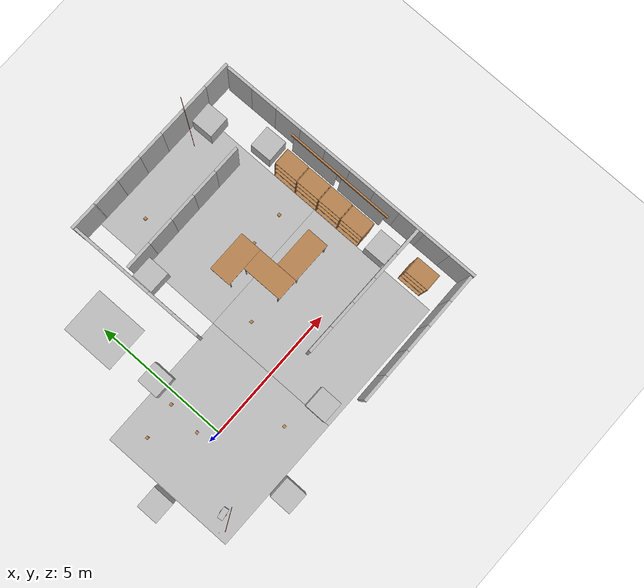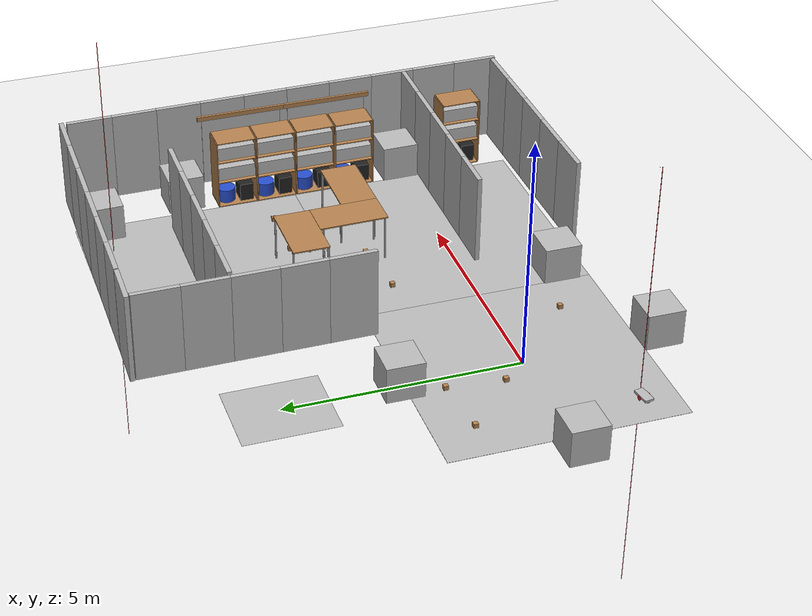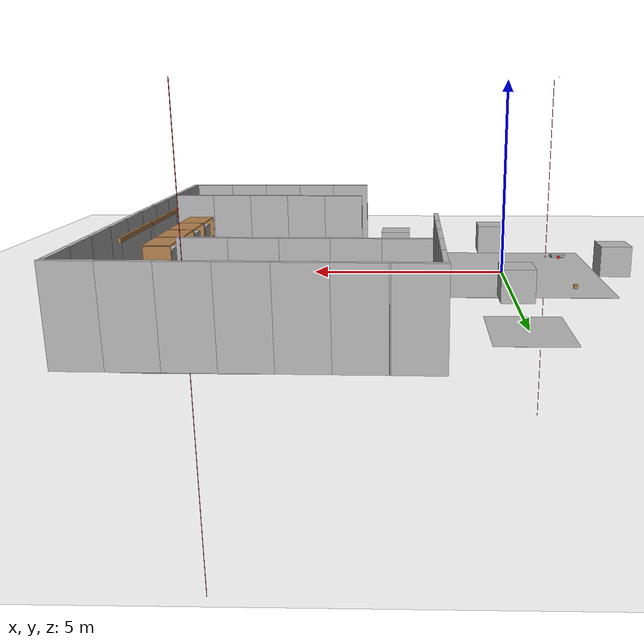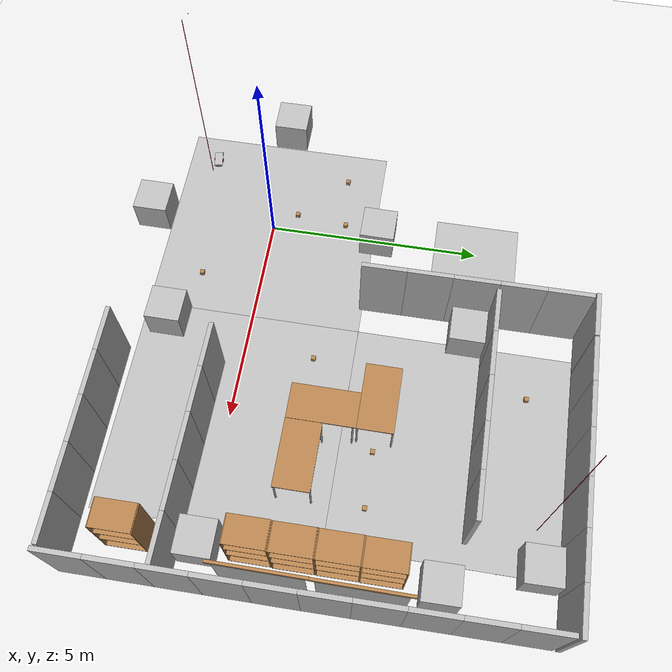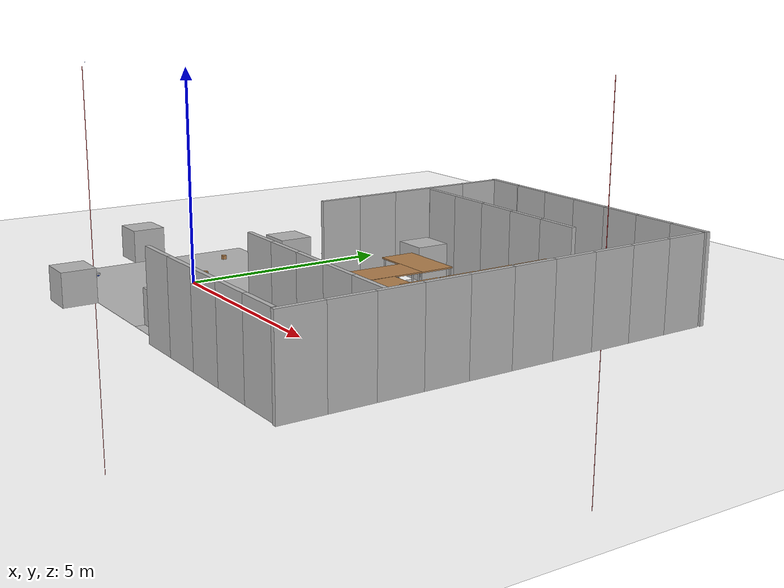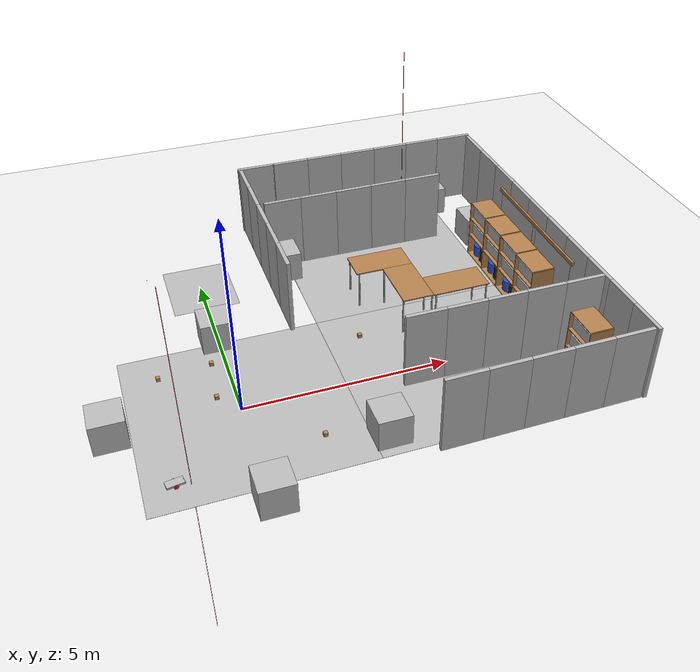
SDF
<sdf version="1.7">
 <world name="default">
  <light name="sun" type="directional">
   <pose>0 0 10 0 -0 0</pose>
   <diffuse>0.8 0.8 0.8 1</diffuse>
   <specular>0.2 0.2 0.2 1</specular>
   <attenuation>
    <range>1000</range>
    <constant>0.9</constant>
    <linear>0.01</linear>
    <quadratic>0.001</quadratic>
   </attenuation>
   <direction>-0.5 0.1 -0.9</direction>
   <spot><inner_angle>0</inner_angle><outer_angle>0</outer_angle><falloff>0</falloff></spot>
  </light>
  <model name="ground_plane">
   <static>1</static>
   <link name="link">
    <collision name="collision">
     <geometry><plane><normal>0 0 1</normal><size>100 100</size></plane></geometry>
     <surface><friction><ode><mu>100</mu><mu2>50</mu2></ode></friction></surface>
    </collision>
    <visual name="visual">
     <cast_shadows>0</cast_shadows>
     <geometry><plane><normal>0 0 1</normal><size>100 100</size></plane></geometry>
     <material>
      <script><uri>file://media/materials/scripts/gazebo.material</uri><name>Gazebo/Grey</name></script>
     </material>
    </visual>
   </link>
  </model>
  <model name="line_flooring">
   <link name="link">
    <collision name="collision">
     <geometry><plane><normal>0 0 1</normal><size>5 5</size></plane></geometry>
     <surface><friction><ode><mu>100</mu><mu2>50</mu2></ode></friction></surface>
    </collision>
    <visual name="visual">
     <geometry><plane><normal>0 0 1</normal><size>5 5</size></plane></geometry>
     <material>
      <script>
       <uri>model://env_line_flooring/materials/test_texture.material</uri>
       <name>LineFlooringTexture</name>
      </script>
     </material>
    </visual>
   </link>
   <pose>0 0 0.001 0 -0 0</pose>
   <static>1</static>
  </model>
  <model name="line_flooring2">
   <link name="link">
    <collision name="collision">
     <geometry><plane><normal>0 0 1</normal><size>5 5</size></plane></geometry>
     <surface><friction><ode><mu>100</mu><mu2>50</mu2></ode></friction></surface>
    </collision>
    <visual name="visual">
     <geometry><plane><normal>0 0 1</normal><size>5 5</size></plane></geometry>
     <material>
      <script>
       <uri>model://env_line_flooring/materials/test_texture.material</uri>
       <name>LineFlooringTexture</name>
      </script>
     </material>
    </visual>
   </link>
   <pose>5 0 0.001 0 -0 0</pose>
   <static>1</static>
  </model>
  <model name="line_flooring3">
   <link name="link">
    <collision name="collision">
     <geometry><plane><normal>0 0 1</normal><size>5 5</size></plane></geometry>
     <surface><friction><ode><mu>100</mu><mu2>50</mu2></ode></friction></surface>
    </collision>
    <visual name="visual">
     <geometry><plane><normal>0 0 1</normal><size>5 5</size></plane></geometry>
     <material>
      <script>
       <uri>model://env_line_flooring/materials/test_texture.material</uri>
       <name>LineFlooringTexture</name>
      </script>
     </material>
    </visual>
   </link>
   <pose>5 5 0.001 0 -0 3.1415</pose>
   <static>1</static>
  </model>
  <scene><ambient>0.6 0.6 0.6 1</ambient><background>0.6 0.6 0.6 1</background><shadows>1</shadows></scene>
  <physics type="ode">
   <max_step_size>0.005</max_step_size>
   <real_time_factor>1</real_time_factor>
   <real_time_update_rate>200</real_time_update_rate>
  </physics>
  <gravity>0 0 -9.8</gravity>
  <magnetic_field>6e-06 2.3e-05 -4.2e-05</magnetic_field>
  <atmosphere type="adiabatic"/>
  <spherical_coordinates>
   <surface_model>EARTH_WGS84</surface_model>
   <latitude_deg>0</latitude_deg>
   <longitude_deg>0</longitude_deg>
   <elevation>0</elevation>
   <heading_deg>0</heading_deg>
  </spherical_coordinates>
  <model name="table">
   <static>1</static>
   <link name="link">
    <collision name="surface">
     <pose>0 0 1 0 -0 0</pose>
     <geometry><box><size>1.5 0.8 0.03</size></box></geometry>
     <surface><friction><ode><mu>0.6</mu><mu2>0.6</mu2></ode></friction></surface>
    </collision>
    <visual name="visual1">
     <pose>0 0 1 0 -0 0</pose>
     <geometry><box><size>1.5 0.8 0.03</size></box></geometry>
     <material>
      <script><uri>file://media/materials/scripts/gazebo.material</uri><name>Gazebo/Wood</name></script>
     </material>
    </visual>
    <collision name="front_left_leg">
     <pose>0.68 0.38 0.5 0 -0 0</pose>
     <geometry><cylinder><radius>0.02</radius><length>1</length></cylinder></geometry>
    </collision>
    <visual name="front_left_leg">
     <pose>0.68 0.38 0.5 0 -0 0</pose>
     <geometry><cylinder><radius>0.02</radius><length>1</length></cylinder></geometry>
     <material>
      <script><uri>file://media/materials/scripts/gazebo.material</uri><name>Gazebo/Grey</name></script>
     </material>
    </visual>
    <collision name="front_right_leg">
     <pose>0.68 -0.38 0.5 0 -0 0</pose>
     <geometry><cylinder><radius>0.02</radius><length>1</length></cylinder></geometry>
    </collision>
    <visual name="front_right_leg">
     <pose>0.68 -0.38 0.5 0 -0 0</pose>
     <geometry><cylinder><radius>0.02</radius><length>1</length></cylinder></geometry>
     <material>
      <script><uri>file://media/materials/scripts/gazebo.material</uri><name>Gazebo/Grey</name></script>
     </material>
    </visual>
    <collision name="back_right_leg">
     <pose>-0.68 -0.38 0.5 0 -0 0</pose>
     <geometry><cylinder><radius>0.02</radius><length>1</length></cylinder></geometry>
    </collision>
    <visual name="back_right_leg">
     <pose>-0.68 -0.38 0.5 0 -0 0</pose>
     <geometry><cylinder><radius>0.02</radius><length>1</length></cylinder></geometry>
     <material>
      <script><uri>file://media/materials/scripts/gazebo.material</uri><name>Gazebo/Grey</name></script>
     </material>
    </visual>
    <collision name="back_left_leg">
     <pose>-0.68 0.38 0.5 0 -0 0</pose>
     <geometry><cylinder><radius>0.02</radius><length>1</length></cylinder></geometry>
    </collision>
    <visual name="back_left_leg">
     <pose>-0.68 0.38 0.5 0 -0 0</pose>
     <geometry><cylinder><radius>0.02</radius><length>1</length></cylinder></geometry>
     <material>
      <script><uri>file://media/materials/scripts/gazebo.material</uri><name>Gazebo/Grey</name></script>
     </material>
    </visual>
   </link>
   <pose>4.81799 2.07912 0.010412 -4.7e-05 -0.009088 -1.56892</pose>
  </model>
  <model name="wood_cube_10cm">
   <link name="link">
    <pose>0 0 0.05 0 -0 0</pose>
    <inertial>
     <mass>0.5167</mass>
     <inertia>
      <ixx>0.000861167</ixx>
      <ixy>0</ixy>
      <ixz>0</ixz>
      <iyy>0.000861167</iyy>
      <iyz>0</iyz>
      <izz>0.000861167</izz>
     </inertia>
    </inertial>
    <collision name="collision">
     <geometry><box><size>0.1 0.1 0.1</size></box></geometry>
     <surface>
      <contact>
       <poissons_ratio>0.347</poissons_ratio>
       <elastic_modulus>8.8e+09</elastic_modulus>
       <ode><kp>100000</kp><kd>100</kd><max_vel>100</max_vel><min_depth>0.001</min_depth></ode>
      </contact>
      <friction>
       <torsional>
        <coefficient>1</coefficient>
        <use_patch_radius>0</use_patch_radius>
        <surface_radius>0.01</surface_radius>
       </torsional>
      </friction>
     </surface>
    </collision>
    <visual name="visual">
     <geometry><box><size>0.1 0.1 0.1</size></box></geometry>
     <material>
      <script><uri>file://media/materials/scripts/gazebo.material</uri><name>Gazebo/Wood</name></script>
     </material>
    </visual>
   </link>
   <pose>1.54178 -1.4356 -3e-06 1e-06 -3e-06 -1e-06</pose>
  </model>
  <model name="env_large_room">
   <link name="base">
    <inertial>
     <mass>100</mass>
     <inertia><ixx>33.4</ixx><ixy>0</ixy><ixz>0</ixz><iyy>41.7</iyy><iyz>0</iyz><izz>8.42</izz></inertia>
    </inertial>
    <collision name="collision1">
     <pose>-2 0 0 0 -0 0</pose>
     <geometry><box><size>1 0.1 2</size></box></geometry>
    </collision>
    <collision name="collision2">
     <pose>-1 0 0 0 -0 0</pose>
     <geometry><box><size>1 0.1 2</size></box></geometry>
    </collision>
    <collision name="collision3"><geometry><box><size>1 0.1 2</size></box></geometry></collision>
    <collision name="collision4">
     <pose>1 0 0 0 -0 0</pose>
     <geometry><box><size>1 0.1 2</size></box></geometry>
    </collision>
    <collision name="collision5">
     <pose>2 0 0 0 -0 0</pose>
     <geometry><box><size>1 0.1 2</size></box></geometry>
    </collision>
    <visual name="visual1">
     <pose>-2 0 0 0 -0 0</pose>
     <geometry><box><size>1 0.1 2</size></box></geometry>
     <material>
      <script><uri>model://env_wall/materials/test_texture.material</uri><name>WallTexture01</name></script>
     </material>
    </visual>
    <visual name="visual2">
     <pose>-1 0 0 0 -0 0</pose>
     <geometry><box><size>1 0.1 2</size></box></geometry>
     <material>
      <script><uri>model://env_wall/materials/test_texture.material</uri><name>WallTexture01</name></script>
     </material>
    </visual>
    <visual name="visual3">
     <geometry><box><size>1 0.1 2</size></box></geometry>
     <material>
      <script><uri>model://env_wall/materials/test_texture.material</uri><name>WallTexture01</name></script>
     </material>
    </visual>
    <visual name="visual4">
     <pose>1 0 0 0 -0 0</pose>
     <geometry><box><size>1 0.1 2</size></box></geometry>
     <material>
      <script><uri>model://env_wall/materials/test_texture.material</uri><name>WallTexture01</name></script>
     </material>
    </visual>
    <visual name="visual5">
     <pose>2 0 0 0 -0 0</pose>
     <geometry><box><size>1 0.1 2</size></box></geometry>
     <material>
      <script><uri>model://env_wall/materials/test_texture.material</uri><name>WallTexture01</name></script>
     </material>
    </visual>
   </link>
   <pose>4.49859 5.40134 1.0008 -6e-06 -0 -0.002793</pose>
  </model>
  <model name="env_wood_shelf">
   <link name="base">
    <inertial>
     <pose>0 0 0.8 0 -0 0</pose>
     <mass>100</mass>
     <inertia><ixx>33.4</ixx><ixy>0</ixy><ixz>0</ixz><iyy>41.7</iyy><iyz>0</iyz><izz>8.42</izz></inertia>
    </inertial>
    <collision name="collision_bottom">
     <pose>0 0 0.01 0 -0 0</pose>
     <geometry><box><size>0.6 0.9 0.02</size></box></geometry>
    </collision>
    <visual name="visual_bottom">
     <pose>0 0 0.01 0 -0 0</pose>
     <geometry><box><size>0.6 0.9 0.02</size></box></geometry>
     <material>
      <script><uri>model://env_wood_shelf/materials/test_texture.material</uri><name>WoodTecture1</name></script>
     </material>
    </visual>
    <collision name="collision_middle1">
     <pose>0 0 0.61 0 -0 0</pose>
     <geometry><box><size>0.6 0.86 0.02</size></box></geometry>
    </collision>
    <visual name="visual_middle1">
     <pose>0 0 0.61 0 -0 0</pose>
     <geometry><box><size>0.6 0.86 0.02</size></box></geometry>
     <material>
      <script><uri>model://env_wood_shelf/materials/test_texture.material</uri><name>WoodTecture1</name></script>
     </material>
    </visual>
    <collision name="collision_middle2">
     <pose>0 0 1.11 0 -0 0</pose>
     <geometry><box><size>0.6 0.86 0.02</size></box></geometry>
    </collision>
    <visual name="visual_middle2">
     <pose>0 0 1.11 0 -0 0</pose>
     <geometry><box><size>0.6 0.86 0.02</size></box></geometry>
     <material>
      <script><uri>model://env_wood_shelf/materials/test_texture.material</uri><name>WoodTecture1</name></script>
     </material>
    </visual>
    <collision name="collision_top">
     <pose>0 0 1.59 0 -0 0</pose>
     <geometry><box><size>0.6 0.86 0.02</size></box></geometry>
    </collision>
    <visual name="visual_top">
     <pose>0 0 1.59 0 -0 0</pose>
     <geometry><box><size>0.6 0.86 0.02</size></box></geometry>
     <material>
      <script><uri>model://env_wood_shelf/materials/test_texture.material</uri><name>WoodTecture1</name></script>
     </material>
    </visual>
    <collision name="collision_right">
     <pose>0 0.44 0.8 0 -0 0</pose>
     <geometry><box><size>0.6 0.02 1.56</size></box></geometry>
    </collision>
    <visual name="visual_right">
     <pose>0 0.44 0.8 0 1.5707 0</pose>
     <geometry><box><size>1.56 0.02 0.6</size></box></geometry>
     <material>
      <script><uri>model://env_wood_shelf/materials/test_texture.material</uri><name>WoodTecture1</name></script>
     </material>
    </visual>
    <collision name="collision_left">
     <pose>0 -0.44 0.8 0 -0 0</pose>
     <geometry><box><size>0.6 0.02 1.56</size></box></geometry>
    </collision>
    <visual name="visual_left">
     <pose>0 -0.44 0.8 0 1.5707 0</pose>
     <geometry><box><size>1.56 0.02 0.6</size></box></geometry>
     <material>
      <script><uri>model://env_wood_shelf/materials/test_texture.material</uri><name>WoodTecture1</name></script>
     </material>
    </visual>
    <collision name="collision_box">
     <pose>0 -0.22 0.22 0 -0 0</pose>
     <geometry><box><size>0.4 0.3 0.4</size></box></geometry>
    </collision>
    <visual name="visual_box">
     <pose>0 -0.22 0.22 0 -0 0</pose>
     <geometry><box><size>0.4 0.3 0.4</size></box></geometry>
     <material>
      <script>
       <uri>model://env_wood_shelf/materials/test_texture.material</uri>
       <name>PlasticBlackTexture</name>
      </script>
     </material>
    </visual>
    <collision name="collision_cylinder">
     <pose>0 0.2 0.17 0 -0 0</pose>
     <geometry><cylinder><radius>0.2</radius><length>0.3</length></cylinder></geometry>
    </collision>
    <visual name="visual_cylinder">
     <pose>0 0.2 0.17 0 -0 0</pose>
     <geometry><cylinder><radius>0.2</radius><length>0.3</length></cylinder></geometry>
     <material>
      <script>
       <uri>model://env_wood_shelf/materials/test_texture.material</uri>
       <name>PlasticBlueTexture</name>
      </script>
     </material>
    </visual>
    <collision name="collision_book1">
     <pose>0 0 0.77 0 -0 0</pose>
     <geometry><box><size>0.4 0.86 0.3</size></box></geometry>
    </collision>
    <visual name="visual_books1">
     <pose>0 0 0.77 0 -0 0</pose>
     <geometry><box><size>0.4 0.86 0.3</size></box></geometry>
     <material>
      <script><uri>model://env_wood_shelf/materials/test_texture.material</uri><name>Books1Texture</name></script>
     </material>
    </visual>
    <collision name="collision_book2">
     <pose>0 0 1.27 0 -0 0</pose>
     <geometry><box><size>0.4 0.86 0.3</size></box></geometry>
    </collision>
    <visual name="visual_books2">
     <pose>0 0 1.27 0 -0 0</pose>
     <geometry><box><size>0.4 0.86 0.3</size></box></geometry>
     <material>
      <script><uri>model://env_wood_shelf/materials/test_texture.material</uri><name>Books2Texture</name></script>
     </material>
    </visual>
   </link>
   <pose>7.90553 -1.47724 0.00095 -8.4e-05 -4e-05 0.007382</pose>
  </model>
  <model name="env_large_room_0">
   <link name="base">
    <inertial>
     <mass>100</mass>
     <inertia><ixx>33.4</ixx><ixy>0</ixy><ixz>0</ixz><iyy>41.7</iyy><iyz>0</iyz><izz>8.42</izz></inertia>
    </inertial>
    <collision name="collision1">
     <pose>-2 0 0 0 -0 0</pose>
     <geometry><box><size>1 0.1 2</size></box></geometry>
    </collision>
    <collision name="collision2">
     <pose>-1 0 0 0 -0 0</pose>
     <geometry><box><size>1 0.1 2</size></box></geometry>
    </collision>
    <collision name="collision3"><geometry><box><size>1 0.1 2</size></box></geometry></collision>
    <collision name="collision4">
     <pose>1 0 0 0 -0 0</pose>
     <geometry><box><size>1 0.1 2</size></box></geometry>
    </collision>
    <collision name="collision5">
     <pose>2 0 0 0 -0 0</pose>
     <geometry><box><size>1 0.1 2</size></box></geometry>
    </collision>
    <visual name="visual1">
     <pose>-2 0 0 0 -0 0</pose>
     <geometry><box><size>1 0.1 2</size></box></geometry>
     <material>
      <script><uri>model://env_wall/materials/test_texture.material</uri><name>WallTexture01</name></script>
     </material>
    </visual>
    <visual name="visual2">
     <pose>-1 0 0 0 -0 0</pose>
     <geometry><box><size>1 0.1 2</size></box></geometry>
     <material>
      <script><uri>model://env_wall/materials/test_texture.material</uri><name>WallTexture01</name></script>
     </material>
    </visual>
    <visual name="visual3">
     <geometry><box><size>1 0.1 2</size></box></geometry>
     <material>
      <script><uri>model://env_wall/materials/test_texture.material</uri><name>WallTexture01</name></script>
     </material>
    </visual>
    <visual name="visual4">
     <pose>1 0 0 0 -0 0</pose>
     <geometry><box><size>1 0.1 2</size></box></geometry>
     <material>
      <script><uri>model://env_wall/materials/test_texture.material</uri><name>WallTexture01</name></script>
     </material>
    </visual>
    <visual name="visual5">
     <pose>2 0 0 0 -0 0</pose>
     <geometry><box><size>1 0.1 2</size></box></geometry>
     <material>
      <script><uri>model://env_wall/materials/test_texture.material</uri><name>WallTexture01</name></script>
     </material>
    </visual>
   </link>
   <pose>6.25772 -0.460538 1.001 4e-06 -4e-06 -0.006764</pose>
  </model>
  <model name="env_large_room_1">
   <link name="base">
    <inertial>
     <mass>100</mass>
     <inertia><ixx>33.4</ixx><ixy>0</ixy><ixz>0</ixz><iyy>41.7</iyy><iyz>0</iyz><izz>8.42</izz></inertia>
    </inertial>
    <collision name="collision1">
     <pose>-2 0 0 0 -0 0</pose>
     <geometry><box><size>1 0.1 2</size></box></geometry>
    </collision>
    <collision name="collision2">
     <pose>-1 0 0 0 -0 0</pose>
     <geometry><box><size>1 0.1 2</size></box></geometry>
    </collision>
    <collision name="collision3"><geometry><box><size>1 0.1 2</size></box></geometry></collision>
    <collision name="collision4">
     <pose>1 0 0 0 -0 0</pose>
     <geometry><box><size>1 0.1 2</size></box></geometry>
    </collision>
    <collision name="collision5">
     <pose>2 0 0 0 -0 0</pose>
     <geometry><box><size>1 0.1 2</size></box></geometry>
    </collision>
    <visual name="visual1">
     <pose>-2 0 0 0 -0 0</pose>
     <geometry><box><size>1 0.1 2</size></box></geometry>
     <material>
      <script><uri>model://env_wall/materials/test_texture.material</uri><name>WallTexture01</name></script>
     </material>
    </visual>
    <visual name="visual2">
     <pose>-1 0 0 0 -0 0</pose>
     <geometry><box><size>1 0.1 2</size></box></geometry>
     <material>
      <script><uri>model://env_wall/materials/test_texture.material</uri><name>WallTexture01</name></script>
     </material>
    </visual>
    <visual name="visual3">
     <geometry><box><size>1 0.1 2</size></box></geometry>
     <material>
      <script><uri>model://env_wall/materials/test_texture.material</uri><name>WallTexture01</name></script>
     </material>
    </visual>
    <visual name="visual4">
     <pose>1 0 0 0 -0 0</pose>
     <geometry><box><size>1 0.1 2</size></box></geometry>
     <material>
      <script><uri>model://env_wall/materials/test_texture.material</uri><name>WallTexture01</name></script>
     </material>
    </visual>
    <visual name="visual5">
     <pose>2 0 0 0 -0 0</pose>
     <geometry><box><size>1 0.1 2</size></box></geometry>
     <material>
      <script><uri>model://env_wall/materials/test_texture.material</uri><name>WallTexture01</name></script>
     </material>
    </visual>
   </link>
   <pose>8.80677 -0.207575 1.00097 1.2e-05 -6.5e-05 -1.56527</pose>
  </model>
  <model name="env_large_room_2">
   <link name="base">
    <inertial>
     <mass>100</mass>
     <inertia><ixx>33.4</ixx><ixy>0</ixy><ixz>0</ixz><iyy>41.7</iyy><iyz>0</iyz><izz>8.42</izz></inertia>
    </inertial>
    <collision name="collision1">
     <pose>-2 0 0 0 -0 0</pose>
     <geometry><box><size>1 0.1 2</size></box></geometry>
    </collision>
    <collision name="collision2">
     <pose>-1 0 0 0 -0 0</pose>
     <geometry><box><size>1 0.1 2</size></box></geometry>
    </collision>
    <collision name="collision3"><geometry><box><size>1 0.1 2</size></box></geometry></collision>
    <collision name="collision4">
     <pose>1 0 0 0 -0 0</pose>
     <geometry><box><size>1 0.1 2</size></box></geometry>
    </collision>
    <collision name="collision5">
     <pose>2 0 0 0 -0 0</pose>
     <geometry><box><size>1 0.1 2</size></box></geometry>
    </collision>
    <visual name="visual1">
     <pose>-2 0 0 0 -0 0</pose>
     <geometry><box><size>1 0.1 2</size></box></geometry>
     <material>
      <script><uri>model://env_wall/materials/test_texture.material</uri><name>WallTexture01</name></script>
     </material>
    </visual>
    <visual name="visual2">
     <pose>-1 0 0 0 -0 0</pose>
     <geometry><box><size>1 0.1 2</size></box></geometry>
     <material>
      <script><uri>model://env_wall/materials/test_texture.material</uri><name>WallTexture01</name></script>
     </material>
    </visual>
    <visual name="visual3">
     <geometry><box><size>1 0.1 2</size></box></geometry>
     <material>
      <script><uri>model://env_wall/materials/test_texture.material</uri><name>WallTexture01</name></script>
     </material>
    </visual>
    <visual name="visual4">
     <pose>1 0 0 0 -0 0</pose>
     <geometry><box><size>1 0.1 2</size></box></geometry>
     <material>
      <script><uri>model://env_wall/materials/test_texture.material</uri><name>WallTexture01</name></script>
     </material>
    </visual>
    <visual name="visual5">
     <pose>2 0 0 0 -0 0</pose>
     <geometry><box><size>1 0.1 2</size></box></geometry>
     <material>
      <script><uri>model://env_wall/materials/test_texture.material</uri><name>WallTexture01</name></script>
     </material>
    </visual>
   </link>
   <pose>8.76311 4.79233 1.00096 1.9e-05 6.4e-05 -1.55973</pose>
  </model>
  <model name="table_0">
   <static>1</static>
   <link name="link">
    <collision name="surface">
     <pose>0 0 1 0 -0 0</pose>
     <geometry><box><size>1.5 0.8 0.03</size></box></geometry>
     <surface><friction><ode><mu>0.6</mu><mu2>0.6</mu2></ode></friction></surface>
    </collision>
    <visual name="visual1">
     <pose>0 0 1 0 -0 0</pose>
     <geometry><box><size>1.5 0.8 0.03</size></box></geometry>
     <material>
      <script><uri>file://media/materials/scripts/gazebo.material</uri><name>Gazebo/Wood</name></script>
     </material>
    </visual>
    <collision name="front_left_leg">
     <pose>0.68 0.38 0.5 0 -0 0</pose>
     <geometry><cylinder><radius>0.02</radius><length>1</length></cylinder></geometry>
    </collision>
    <visual name="front_left_leg">
     <pose>0.68 0.38 0.5 0 -0 0</pose>
     <geometry><cylinder><radius>0.02</radius><length>1</length></cylinder></geometry>
     <material>
      <script><uri>file://media/materials/scripts/gazebo.material</uri><name>Gazebo/Grey</name></script>
     </material>
    </visual>
    <collision name="front_right_leg">
     <pose>0.68 -0.38 0.5 0 -0 0</pose>
     <geometry><cylinder><radius>0.02</radius><length>1</length></cylinder></geometry>
    </collision>
    <visual name="front_right_leg">
     <pose>0.68 -0.38 0.5 0 -0 0</pose>
     <geometry><cylinder><radius>0.02</radius><length>1</length></cylinder></geometry>
     <material>
      <script><uri>file://media/materials/scripts/gazebo.material</uri><name>Gazebo/Grey</name></script>
     </material>
    </visual>
    <collision name="back_right_leg">
     <pose>-0.68 -0.38 0.5 0 -0 0</pose>
     <geometry><cylinder><radius>0.02</radius><length>1</length></cylinder></geometry>
    </collision>
    <visual name="back_right_leg">
     <pose>-0.68 -0.38 0.5 0 -0 0</pose>
     <geometry><cylinder><radius>0.02</radius><length>1</length></cylinder></geometry>
     <material>
      <script><uri>file://media/materials/scripts/gazebo.material</uri><name>Gazebo/Grey</name></script>
     </material>
    </visual>
    <collision name="back_left_leg">
     <pose>-0.68 0.38 0.5 0 -0 0</pose>
     <geometry><cylinder><radius>0.02</radius><length>1</length></cylinder></geometry>
    </collision>
    <visual name="back_left_leg">
     <pose>-0.68 0.38 0.5 0 -0 0</pose>
     <geometry><cylinder><radius>0.02</radius><length>1</length></cylinder></geometry>
     <material>
      <script><uri>file://media/materials/scripts/gazebo.material</uri><name>Gazebo/Grey</name></script>
     </material>
    </visual>
   </link>
   <pose>4.46738 3.23399 0 0 -0 0</pose>
  </model>
  <model name="env_large_room_6">
   <link name="base">
    <inertial>
     <mass>100</mass>
     <inertia><ixx>33.4</ixx><ixy>0</ixy><ixz>0</ixz><iyy>41.7</iyy><iyz>0</iyz><izz>8.42</izz></inertia>
    </inertial>
    <collision name="collision1">
     <pose>-2 0 0 0 -0 0</pose>
     <geometry><box><size>1 0.1 2</size></box></geometry>
    </collision>
    <collision name="collision2">
     <pose>-1 0 0 0 -0 0</pose>
     <geometry><box><size>1 0.1 2</size></box></geometry>
    </collision>
    <collision name="collision3"><geometry><box><size>1 0.1 2</size></box></geometry></collision>
    <collision name="collision4">
     <pose>1 0 0 0 -0 0</pose>
     <geometry><box><size>1 0.1 2</size></box></geometry>
    </collision>
    <collision name="collision5">
     <pose>2 0 0 0 -0 0</pose>
     <geometry><box><size>1 0.1 2</size></box></geometry>
    </collision>
    <visual name="visual1">
     <pose>-2 0 0 0 -0 0</pose>
     <geometry><box><size>1 0.1 2</size></box></geometry>
     <material>
      <script><uri>model://env_wall/materials/test_texture.material</uri><name>WallTexture01</name></script>
     </material>
    </visual>
    <visual name="visual2">
     <pose>-1 0 0 0 -0 0</pose>
     <geometry><box><size>1 0.1 2</size></box></geometry>
     <material>
      <script><uri>model://env_wall/materials/test_texture.material</uri><name>WallTexture01</name></script>
     </material>
    </visual>
    <visual name="visual3">
     <geometry><box><size>1 0.1 2</size></box></geometry>
     <material>
      <script><uri>model://env_wall/materials/test_texture.material</uri><name>WallTexture01</name></script>
     </material>
    </visual>
    <visual name="visual4">
     <pose>1 0 0 0 -0 0</pose>
     <geometry><box><size>1 0.1 2</size></box></geometry>
     <material>
      <script><uri>model://env_wall/materials/test_texture.material</uri><name>WallTexture01</name></script>
     </material>
    </visual>
    <visual name="visual5">
     <pose>2 0 0 0 -0 0</pose>
     <geometry><box><size>1 0.1 2</size></box></geometry>
     <material>
      <script><uri>model://env_wall/materials/test_texture.material</uri><name>WallTexture01</name></script>
     </material>
    </visual>
   </link>
   <pose>6.24098 -2.64813 1.00079 -8e-06 8.3e-05 0.007746</pose>
  </model>
  <model name="wood_cube_10cm_0">
   <link name="link">
    <pose>0 0 0.05 0 -0 0</pose>
    <inertial>
     <mass>0.5167</mass>
     <inertia>
      <ixx>0.000861167</ixx>
      <ixy>0</ixy>
      <ixz>0</ixz>
      <iyy>0.000861167</iyy>
      <iyz>0</iyz>
      <izz>0.000861167</izz>
     </inertia>
    </inertial>
    <collision name="collision">
     <geometry><box><size>0.1 0.1 0.1</size></box></geometry>
     <surface>
      <contact>
       <poissons_ratio>0.347</poissons_ratio>
       <elastic_modulus>8.8e+09</elastic_modulus>
       <ode><kp>100000</kp><kd>100</kd><max_vel>100</max_vel><min_depth>0.001</min_depth></ode>
      </contact>
      <friction>
       <torsional>
        <coefficient>1</coefficient>
        <use_patch_radius>0</use_patch_radius>
        <surface_radius>0.01</surface_radius>
       </torsional>
      </friction>
     </surface>
    </collision>
    <visual name="visual">
     <geometry><box><size>0.1 0.1 0.1</size></box></geometry>
     <material>
      <script><uri>file://media/materials/scripts/gazebo.material</uri><name>Gazebo/Wood</name></script>
     </material>
    </visual>
   </link>
   <pose>3.59739 6.45566 -3e-06 -1e-06 3e-06 0</pose>
  </model>
  <model name="wood_cube_10cm_1">
   <link name="link">
    <pose>0 0 0.05 0 -0 0</pose>
    <inertial>
     <mass>0.5167</mass>
     <inertia>
      <ixx>0.000861167</ixx>
      <ixy>0</ixy>
      <ixz>0</ixz>
      <iyy>0.000861167</iyy>
      <iyz>0</iyz>
      <izz>0.000861167</izz>
     </inertia>
    </inertial>
    <collision name="collision">
     <geometry><box><size>0.1 0.1 0.1</size></box></geometry>
     <surface>
      <contact>
       <poissons_ratio>0.347</poissons_ratio>
       <elastic_modulus>8.8e+09</elastic_modulus>
       <ode><kp>100000</kp><kd>100</kd><max_vel>100</max_vel><min_depth>0.001</min_depth></ode>
      </contact>
      <friction>
       <torsional>
        <coefficient>1</coefficient>
        <use_patch_radius>0</use_patch_radius>
        <surface_radius>0.01</surface_radius>
       </torsional>
      </friction>
     </surface>
    </collision>
    <visual name="visual">
     <geometry><box><size>0.1 0.1 0.1</size></box></geometry>
     <material>
      <script><uri>file://media/materials/scripts/gazebo.material</uri><name>Gazebo/Wood</name></script>
     </material>
    </visual>
   </link>
   <pose>5.35255 3.24149 -3e-06 -3e-06 1e-06 -1.1e-05</pose>
  </model>
  <model name="wood_cube_10cm_2">
   <link name="link">
    <pose>0 0 0.05 0 -0 0</pose>
    <inertial>
     <mass>0.5167</mass>
     <inertia>
      <ixx>0.000861167</ixx>
      <ixy>0</ixy>
      <ixz>0</ixz>
      <iyy>0.000861167</iyy>
      <iyz>0</iyz>
      <izz>0.000861167</izz>
     </inertia>
    </inertial>
    <collision name="collision">
     <geometry><box><size>0.1 0.1 0.1</size></box></geometry>
     <surface>
      <contact>
       <poissons_ratio>0.347</poissons_ratio>
       <elastic_modulus>8.8e+09</elastic_modulus>
       <ode><kp>100000</kp><kd>100</kd><max_vel>100</max_vel><min_depth>0.001</min_depth></ode>
      </contact>
      <friction>
       <torsional>
        <coefficient>1</coefficient>
        <use_patch_radius>0</use_patch_radius>
        <surface_radius>0.01</surface_radius>
       </torsional>
      </friction>
     </surface>
    </collision>
    <visual name="visual">
     <geometry><box><size>0.1 0.1 0.1</size></box></geometry>
     <material>
      <script><uri>file://media/materials/scripts/gazebo.material</uri><name>Gazebo/Wood</name></script>
     </material>
    </visual>
   </link>
   <pose>3.35972 1.59541 -3e-06 3e-06 -1e-06 0</pose>
  </model>
  <model name="wood_cube_10cm_3">
   <link name="link">
    <pose>0 0 0.05 0 -0 0</pose>
    <inertial>
     <mass>0.5167</mass>
     <inertia>
      <ixx>0.000861167</ixx>
      <ixy>0</ixy>
      <ixz>0</ixz>
      <iyy>0.000861167</iyy>
      <iyz>0</iyz>
      <izz>0.000861167</izz>
     </inertia>
    </inertial>
    <collision name="collision">
     <geometry><box><size>0.1 0.1 0.1</size></box></geometry>
     <surface>
      <contact>
       <poissons_ratio>0.347</poissons_ratio>
       <elastic_modulus>8.8e+09</elastic_modulus>
       <ode><kp>100000</kp><kd>100</kd><max_vel>100</max_vel><min_depth>0.001</min_depth></ode>
      </contact>
      <friction>
       <torsional>
        <coefficient>1</coefficient>
        <use_patch_radius>0</use_patch_radius>
        <surface_radius>0.01</surface_radius>
       </torsional>
      </friction>
     </surface>
    </collision>
    <visual name="visual">
     <geometry><box><size>0.1 0.1 0.1</size></box></geometry>
     <material>
      <script><uri>file://media/materials/scripts/gazebo.material</uri><name>Gazebo/Wood</name></script>
     </material>
    </visual>
   </link>
   <pose>4.70642 1.74347 -3e-06 1e-06 -3e-06 0</pose>
  </model>
  <model name="env_large_room_7">
   <link name="base">
    <inertial>
     <mass>100</mass>
     <inertia><ixx>33.4</ixx><ixy>0</ixy><ixz>0</ixz><iyy>41.7</iyy><iyz>0</iyz><izz>8.42</izz></inertia>
    </inertial>
    <collision name="collision"><geometry><box><size>1 0.1 2</size></box></geometry></collision>
    <visual name="visual">
     <geometry><box><size>1 0.1 2</size></box></geometry>
     <material>
      <script><uri>model://env_wall/materials/test_texture.material</uri><name>WallTexture01</name></script>
     </material>
    </visual>
   </link>
   <pose>2.26778 7.48741 1.00081 7e-06 -0 -0.019106</pose>
  </model>
  <model name="table_1">
   <static>1</static>
   <link name="link">
    <collision name="surface">
     <pose>0 0 1 0 -0 0</pose>
     <geometry><box><size>1.5 0.8 0.03</size></box></geometry>
     <surface><friction><ode><mu>0.6</mu><mu2>0.6</mu2></ode></friction></surface>
    </collision>
    <visual name="visual1">
     <pose>0 0 1 0 -0 0</pose>
     <geometry><box><size>1.5 0.8 0.03</size></box></geometry>
     <material>
      <script><uri>file://media/materials/scripts/gazebo.material</uri><name>Gazebo/Wood</name></script>
     </material>
    </visual>
    <collision name="front_left_leg">
     <pose>0.68 0.38 0.5 0 -0 0</pose>
     <geometry><cylinder><radius>0.02</radius><length>1</length></cylinder></geometry>
    </collision>
    <visual name="front_left_leg">
     <pose>0.68 0.38 0.5 0 -0 0</pose>
     <geometry><cylinder><radius>0.02</radius><length>1</length></cylinder></geometry>
     <material>
      <script><uri>file://media/materials/scripts/gazebo.material</uri><name>Gazebo/Grey</name></script>
     </material>
    </visual>
    <collision name="front_right_leg">
     <pose>0.68 -0.38 0.5 0 -0 0</pose>
     <geometry><cylinder><radius>0.02</radius><length>1</length></cylinder></geometry>
    </collision>
    <visual name="front_right_leg">
     <pose>0.68 -0.38 0.5 0 -0 0</pose>
     <geometry><cylinder><radius>0.02</radius><length>1</length></cylinder></geometry>
     <material>
      <script><uri>file://media/materials/scripts/gazebo.material</uri><name>Gazebo/Grey</name></script>
     </material>
    </visual>
    <collision name="back_right_leg">
     <pose>-0.68 -0.38 0.5 0 -0 0</pose>
     <geometry><cylinder><radius>0.02</radius><length>1</length></cylinder></geometry>
    </collision>
    <visual name="back_right_leg">
     <pose>-0.68 -0.38 0.5 0 -0 0</pose>
     <geometry><cylinder><radius>0.02</radius><length>1</length></cylinder></geometry>
     <material>
      <script><uri>file://media/materials/scripts/gazebo.material</uri><name>Gazebo/Grey</name></script>
     </material>
    </visual>
    <collision name="back_left_leg">
     <pose>-0.68 0.38 0.5 0 -0 0</pose>
     <geometry><cylinder><radius>0.02</radius><length>1</length></cylinder></geometry>
    </collision>
    <visual name="back_left_leg">
     <pose>-0.68 0.38 0.5 0 -0 0</pose>
     <geometry><cylinder><radius>0.02</radius><length>1</length></cylinder></geometry>
     <material>
      <script><uri>file://media/materials/scripts/gazebo.material</uri><name>Gazebo/Grey</name></script>
     </material>
    </visual>
   </link>
   <pose>5.96965 1.73408 0.006674 0 -0 0</pose>
  </model>
  <model name="env_wood_shelf_1">
   <link name="base">
    <inertial>
     <pose>0 0 0.8 0 -0 0</pose>
     <mass>100</mass>
     <inertia><ixx>33.4</ixx><ixy>0</ixy><ixz>0</ixz><iyy>41.7</iyy><iyz>0</iyz><izz>8.42</izz></inertia>
    </inertial>
    <collision name="collision_bottom">
     <pose>0 0 0.01 0 -0 0</pose>
     <geometry><box><size>0.6 0.9 0.02</size></box></geometry>
    </collision>
    <visual name="visual_bottom">
     <pose>0 0 0.01 0 -0 0</pose>
     <geometry><box><size>0.6 0.9 0.02</size></box></geometry>
     <material>
      <script><uri>model://env_wood_shelf/materials/test_texture.material</uri><name>WoodTecture1</name></script>
     </material>
    </visual>
    <collision name="collision_middle1">
     <pose>0 0 0.61 0 -0 0</pose>
     <geometry><box><size>0.6 0.86 0.02</size></box></geometry>
    </collision>
    <visual name="visual_middle1">
     <pose>0 0 0.61 0 -0 0</pose>
     <geometry><box><size>0.6 0.86 0.02</size></box></geometry>
     <material>
      <script><uri>model://env_wood_shelf/materials/test_texture.material</uri><name>WoodTecture1</name></script>
     </material>
    </visual>
    <collision name="collision_middle2">
     <pose>0 0 1.11 0 -0 0</pose>
     <geometry><box><size>0.6 0.86 0.02</size></box></geometry>
    </collision>
    <visual name="visual_middle2">
     <pose>0 0 1.11 0 -0 0</pose>
     <geometry><box><size>0.6 0.86 0.02</size></box></geometry>
     <material>
      <script><uri>model://env_wood_shelf/materials/test_texture.material</uri><name>WoodTecture1</name></script>
     </material>
    </visual>
    <collision name="collision_top">
     <pose>0 0 1.59 0 -0 0</pose>
     <geometry><box><size>0.6 0.86 0.02</size></box></geometry>
    </collision>
    <visual name="visual_top">
     <pose>0 0 1.59 0 -0 0</pose>
     <geometry><box><size>0.6 0.86 0.02</size></box></geometry>
     <material>
      <script><uri>model://env_wood_shelf/materials/test_texture.material</uri><name>WoodTecture1</name></script>
     </material>
    </visual>
    <collision name="collision_right">
     <pose>0 0.44 0.8 0 -0 0</pose>
     <geometry><box><size>0.6 0.02 1.56</size></box></geometry>
    </collision>
    <visual name="visual_right">
     <pose>0 0.44 0.8 0 1.5707 0</pose>
     <geometry><box><size>1.56 0.02 0.6</size></box></geometry>
     <material>
      <script><uri>model://env_wood_shelf/materials/test_texture.material</uri><name>WoodTecture1</name></script>
     </material>
    </visual>
    <collision name="collision_left">
     <pose>0 -0.44 0.8 0 -0 0</pose>
     <geometry><box><size>0.6 0.02 1.56</size></box></geometry>
    </collision>
    <visual name="visual_left">
     <pose>0 -0.44 0.8 0 1.5707 0</pose>
     <geometry><box><size>1.56 0.02 0.6</size></box></geometry>
     <material>
      <script><uri>model://env_wood_shelf/materials/test_texture.material</uri><name>WoodTecture1</name></script>
     </material>
    </visual>
    <collision name="collision_box">
     <pose>0 -0.22 0.22 0 -0 0</pose>
     <geometry><box><size>0.4 0.3 0.4</size></box></geometry>
    </collision>
    <visual name="visual_box">
     <pose>0 -0.22 0.22 0 -0 0</pose>
     <geometry><box><size>0.4 0.3 0.4</size></box></geometry>
     <material>
      <script>
       <uri>model://env_wood_shelf/materials/test_texture.material</uri>
       <name>PlasticBlackTexture</name>
      </script>
     </material>
    </visual>
    <collision name="collision_cylinder">
     <pose>0 0.2 0.17 0 -0 0</pose>
     <geometry><cylinder><radius>0.2</radius><length>0.3</length></cylinder></geometry>
    </collision>
    <visual name="visual_cylinder">
     <pose>0 0.2 0.17 0 -0 0</pose>
     <geometry><cylinder><radius>0.2</radius><length>0.3</length></cylinder></geometry>
     <material>
      <script>
       <uri>model://env_wood_shelf/materials/test_texture.material</uri>
       <name>PlasticBlueTexture</name>
      </script>
     </material>
    </visual>
    <collision name="collision_book1">
     <pose>0 0 0.77 0 -0 0</pose>
     <geometry><box><size>0.4 0.86 0.3</size></box></geometry>
    </collision>
    <visual name="visual_books1">
     <pose>0 0 0.77 0 -0 0</pose>
     <geometry><box><size>0.4 0.86 0.3</size></box></geometry>
     <material>
      <script><uri>model://env_wood_shelf/materials/test_texture.material</uri><name>Books1Texture</name></script>
     </material>
    </visual>
    <collision name="collision_book2">
     <pose>0 0 1.27 0 -0 0</pose>
     <geometry><box><size>0.4 0.86 0.3</size></box></geometry>
    </collision>
    <visual name="visual_books2">
     <pose>0 0 1.27 0 -0 0</pose>
     <geometry><box><size>0.4 0.86 0.3</size></box></geometry>
     <material>
      <script><uri>model://env_wood_shelf/materials/test_texture.material</uri><name>Books2Texture</name></script>
     </material>
    </visual>
   </link>
   <pose>7.8062 3.80779 0.001007 -1.7e-05 -1e-06 0.009206</pose>
  </model>
  <model name="env_wood_shelf_2">
   <link name="base">
    <inertial>
     <pose>0 0 0.8 0 -0 0</pose>
     <mass>100</mass>
     <inertia><ixx>33.4</ixx><ixy>0</ixy><ixz>0</ixz><iyy>41.7</iyy><iyz>0</iyz><izz>8.42</izz></inertia>
    </inertial>
    <collision name="collision_bottom">
     <pose>0 0 0.01 0 -0 0</pose>
     <geometry><box><size>0.6 0.9 0.02</size></box></geometry>
    </collision>
    <visual name="visual_bottom">
     <pose>0 0 0.01 0 -0 0</pose>
     <geometry><box><size>0.6 0.9 0.02</size></box></geometry>
     <material>
      <script><uri>model://env_wood_shelf/materials/test_texture.material</uri><name>WoodTecture1</name></script>
     </material>
    </visual>
    <collision name="collision_middle1">
     <pose>0 0 0.61 0 -0 0</pose>
     <geometry><box><size>0.6 0.86 0.02</size></box></geometry>
    </collision>
    <visual name="visual_middle1">
     <pose>0 0 0.61 0 -0 0</pose>
     <geometry><box><size>0.6 0.86 0.02</size></box></geometry>
     <material>
      <script><uri>model://env_wood_shelf/materials/test_texture.material</uri><name>WoodTecture1</name></script>
     </material>
    </visual>
    <collision name="collision_middle2">
     <pose>0 0 1.11 0 -0 0</pose>
     <geometry><box><size>0.6 0.86 0.02</size></box></geometry>
    </collision>
    <visual name="visual_middle2">
     <pose>0 0 1.11 0 -0 0</pose>
     <geometry><box><size>0.6 0.86 0.02</size></box></geometry>
     <material>
      <script><uri>model://env_wood_shelf/materials/test_texture.material</uri><name>WoodTecture1</name></script>
     </material>
    </visual>
    <collision name="collision_top">
     <pose>0 0 1.59 0 -0 0</pose>
     <geometry><box><size>0.6 0.86 0.02</size></box></geometry>
    </collision>
    <visual name="visual_top">
     <pose>0 0 1.59 0 -0 0</pose>
     <geometry><box><size>0.6 0.86 0.02</size></box></geometry>
     <material>
      <script><uri>model://env_wood_shelf/materials/test_texture.material</uri><name>WoodTecture1</name></script>
     </material>
    </visual>
    <collision name="collision_right">
     <pose>0 0.44 0.8 0 -0 0</pose>
     <geometry><box><size>0.6 0.02 1.56</size></box></geometry>
    </collision>
    <visual name="visual_right">
     <pose>0 0.44 0.8 0 1.5707 0</pose>
     <geometry><box><size>1.56 0.02 0.6</size></box></geometry>
     <material>
      <script><uri>model://env_wood_shelf/materials/test_texture.material</uri><name>WoodTecture1</name></script>
     </material>
    </visual>
    <collision name="collision_left">
     <pose>0 -0.44 0.8 0 -0 0</pose>
     <geometry><box><size>0.6 0.02 1.56</size></box></geometry>
    </collision>
    <visual name="visual_left">
     <pose>0 -0.44 0.8 0 1.5707 0</pose>
     <geometry><box><size>1.56 0.02 0.6</size></box></geometry>
     <material>
      <script><uri>model://env_wood_shelf/materials/test_texture.material</uri><name>WoodTecture1</name></script>
     </material>
    </visual>
    <collision name="collision_box">
     <pose>0 -0.22 0.22 0 -0 0</pose>
     <geometry><box><size>0.4 0.3 0.4</size></box></geometry>
    </collision>
    <visual name="visual_box">
     <pose>0 -0.22 0.22 0 -0 0</pose>
     <geometry><box><size>0.4 0.3 0.4</size></box></geometry>
     <material>
      <script>
       <uri>model://env_wood_shelf/materials/test_texture.material</uri>
       <name>PlasticBlackTexture</name>
      </script>
     </material>
    </visual>
    <collision name="collision_cylinder">
     <pose>0 0.2 0.17 0 -0 0</pose>
     <geometry><cylinder><radius>0.2</radius><length>0.3</length></cylinder></geometry>
    </collision>
    <visual name="visual_cylinder">
     <pose>0 0.2 0.17 0 -0 0</pose>
     <geometry><cylinder><radius>0.2</radius><length>0.3</length></cylinder></geometry>
     <material>
      <script>
       <uri>model://env_wood_shelf/materials/test_texture.material</uri>
       <name>PlasticBlueTexture</name>
      </script>
     </material>
    </visual>
    <collision name="collision_book1">
     <pose>0 0 0.77 0 -0 0</pose>
     <geometry><box><size>0.4 0.86 0.3</size></box></geometry>
    </collision>
    <visual name="visual_books1">
     <pose>0 0 0.77 0 -0 0</pose>
     <geometry><box><size>0.4 0.86 0.3</size></box></geometry>
     <material>
      <script><uri>model://env_wood_shelf/materials/test_texture.material</uri><name>Books1Texture</name></script>
     </material>
    </visual>
    <collision name="collision_book2">
     <pose>0 0 1.27 0 -0 0</pose>
     <geometry><box><size>0.4 0.86 0.3</size></box></geometry>
    </collision>
    <visual name="visual_books2">
     <pose>0 0 1.27 0 -0 0</pose>
     <geometry><box><size>0.4 0.86 0.3</size></box></geometry>
     <material>
      <script><uri>model://env_wood_shelf/materials/test_texture.material</uri><name>Books2Texture</name></script>
     </material>
    </visual>
   </link>
   <pose>7.80801 2.90775 0.001007 -1.7e-05 -1e-06 0.009146</pose>
  </model>
  <model name="env_wood_shelf_3">
   <link name="base">
    <inertial>
     <pose>0 0 0.8 0 -0 0</pose>
     <mass>100</mass>
     <inertia><ixx>33.4</ixx><ixy>0</ixy><ixz>0</ixz><iyy>41.7</iyy><iyz>0</iyz><izz>8.42</izz></inertia>
    </inertial>
    <collision name="collision_bottom">
     <pose>0 0 0.01 0 -0 0</pose>
     <geometry><box><size>0.6 0.9 0.02</size></box></geometry>
    </collision>
    <visual name="visual_bottom">
     <pose>0 0 0.01 0 -0 0</pose>
     <geometry><box><size>0.6 0.9 0.02</size></box></geometry>
     <material>
      <script><uri>model://env_wood_shelf/materials/test_texture.material</uri><name>WoodTecture1</name></script>
     </material>
    </visual>
    <collision name="collision_middle1">
     <pose>0 0 0.61 0 -0 0</pose>
     <geometry><box><size>0.6 0.86 0.02</size></box></geometry>
    </collision>
    <visual name="visual_middle1">
     <pose>0 0 0.61 0 -0 0</pose>
     <geometry><box><size>0.6 0.86 0.02</size></box></geometry>
     <material>
      <script><uri>model://env_wood_shelf/materials/test_texture.material</uri><name>WoodTecture1</name></script>
     </material>
    </visual>
    <collision name="collision_middle2">
     <pose>0 0 1.11 0 -0 0</pose>
     <geometry><box><size>0.6 0.86 0.02</size></box></geometry>
    </collision>
    <visual name="visual_middle2">
     <pose>0 0 1.11 0 -0 0</pose>
     <geometry><box><size>0.6 0.86 0.02</size></box></geometry>
     <material>
      <script><uri>model://env_wood_shelf/materials/test_texture.material</uri><name>WoodTecture1</name></script>
     </material>
    </visual>
    <collision name="collision_top">
     <pose>0 0 1.59 0 -0 0</pose>
     <geometry><box><size>0.6 0.86 0.02</size></box></geometry>
    </collision>
    <visual name="visual_top">
     <pose>0 0 1.59 0 -0 0</pose>
     <geometry><box><size>0.6 0.86 0.02</size></box></geometry>
     <material>
      <script><uri>model://env_wood_shelf/materials/test_texture.material</uri><name>WoodTecture1</name></script>
     </material>
    </visual>
    <collision name="collision_right">
     <pose>0 0.44 0.8 0 -0 0</pose>
     <geometry><box><size>0.6 0.02 1.56</size></box></geometry>
    </collision>
    <visual name="visual_right">
     <pose>0 0.44 0.8 0 1.5707 0</pose>
     <geometry><box><size>1.56 0.02 0.6</size></box></geometry>
     <material>
      <script><uri>model://env_wood_shelf/materials/test_texture.material</uri><name>WoodTecture1</name></script>
     </material>
    </visual>
    <collision name="collision_left">
     <pose>0 -0.44 0.8 0 -0 0</pose>
     <geometry><box><size>0.6 0.02 1.56</size></box></geometry>
    </collision>
    <visual name="visual_left">
     <pose>0 -0.44 0.8 0 1.5707 0</pose>
     <geometry><box><size>1.56 0.02 0.6</size></box></geometry>
     <material>
      <script><uri>model://env_wood_shelf/materials/test_texture.material</uri><name>WoodTecture1</name></script>
     </material>
    </visual>
    <collision name="collision_box">
     <pose>0 -0.22 0.22 0 -0 0</pose>
     <geometry><box><size>0.4 0.3 0.4</size></box></geometry>
    </collision>
    <visual name="visual_box">
     <pose>0 -0.22 0.22 0 -0 0</pose>
     <geometry><box><size>0.4 0.3 0.4</size></box></geometry>
     <material>
      <script>
       <uri>model://env_wood_shelf/materials/test_texture.material</uri>
       <name>PlasticBlackTexture</name>
      </script>
     </material>
    </visual>
    <collision name="collision_cylinder">
     <pose>0 0.2 0.17 0 -0 0</pose>
     <geometry><cylinder><radius>0.2</radius><length>0.3</length></cylinder></geometry>
    </collision>
    <visual name="visual_cylinder">
     <pose>0 0.2 0.17 0 -0 0</pose>
     <geometry><cylinder><radius>0.2</radius><length>0.3</length></cylinder></geometry>
     <material>
      <script>
       <uri>model://env_wood_shelf/materials/test_texture.material</uri>
       <name>PlasticBlueTexture</name>
      </script>
     </material>
    </visual>
    <collision name="collision_book1">
     <pose>0 0 0.77 0 -0 0</pose>
     <geometry><box><size>0.4 0.86 0.3</size></box></geometry>
    </collision>
    <visual name="visual_books1">
     <pose>0 0 0.77 0 -0 0</pose>
     <geometry><box><size>0.4 0.86 0.3</size></box></geometry>
     <material>
      <script><uri>model://env_wood_shelf/materials/test_texture.material</uri><name>Books1Texture</name></script>
     </material>
    </visual>
    <collision name="collision_book2">
     <pose>0 0 1.27 0 -0 0</pose>
     <geometry><box><size>0.4 0.86 0.3</size></box></geometry>
    </collision>
    <visual name="visual_books2">
     <pose>0 0 1.27 0 -0 0</pose>
     <geometry><box><size>0.4 0.86 0.3</size></box></geometry>
     <material>
      <script><uri>model://env_wood_shelf/materials/test_texture.material</uri><name>Books2Texture</name></script>
     </material>
    </visual>
   </link>
   <pose>7.81145 2.00502 0.00095 -8.4e-05 -4e-05 0.007602</pose>
  </model>
  <model name="env_wood_shelf_4">
   <link name="base">
    <inertial>
     <pose>0 0 0.8 0 -0 0</pose>
     <mass>100</mass>
     <inertia><ixx>33.4</ixx><ixy>0</ixy><ixz>0</ixz><iyy>41.7</iyy><iyz>0</iyz><izz>8.42</izz></inertia>
    </inertial>
    <collision name="collision_bottom">
     <pose>0 0 0.01 0 -0 0</pose>
     <geometry><box><size>0.6 0.9 0.02</size></box></geometry>
    </collision>
    <visual name="visual_bottom">
     <pose>0 0 0.01 0 -0 0</pose>
     <geometry><box><size>0.6 0.9 0.02</size></box></geometry>
     <material>
      <script><uri>model://env_wood_shelf/materials/test_texture.material</uri><name>WoodTecture1</name></script>
     </material>
    </visual>
    <collision name="collision_middle1">
     <pose>0 0 0.61 0 -0 0</pose>
     <geometry><box><size>0.6 0.86 0.02</size></box></geometry>
    </collision>
    <visual name="visual_middle1">
     <pose>0 0 0.61 0 -0 0</pose>
     <geometry><box><size>0.6 0.86 0.02</size></box></geometry>
     <material>
      <script><uri>model://env_wood_shelf/materials/test_texture.material</uri><name>WoodTecture1</name></script>
     </material>
    </visual>
    <collision name="collision_middle2">
     <pose>0 0 1.11 0 -0 0</pose>
     <geometry><box><size>0.6 0.86 0.02</size></box></geometry>
    </collision>
    <visual name="visual_middle2">
     <pose>0 0 1.11 0 -0 0</pose>
     <geometry><box><size>0.6 0.86 0.02</size></box></geometry>
     <material>
      <script><uri>model://env_wood_shelf/materials/test_texture.material</uri><name>WoodTecture1</name></script>
     </material>
    </visual>
    <collision name="collision_top">
     <pose>0 0 1.59 0 -0 0</pose>
     <geometry><box><size>0.6 0.86 0.02</size></box></geometry>
    </collision>
    <visual name="visual_top">
     <pose>0 0 1.59 0 -0 0</pose>
     <geometry><box><size>0.6 0.86 0.02</size></box></geometry>
     <material>
      <script><uri>model://env_wood_shelf/materials/test_texture.material</uri><name>WoodTecture1</name></script>
     </material>
    </visual>
    <collision name="collision_right">
     <pose>0 0.44 0.8 0 -0 0</pose>
     <geometry><box><size>0.6 0.02 1.56</size></box></geometry>
    </collision>
    <visual name="visual_right">
     <pose>0 0.44 0.8 0 1.5707 0</pose>
     <geometry><box><size>1.56 0.02 0.6</size></box></geometry>
     <material>
      <script><uri>model://env_wood_shelf/materials/test_texture.material</uri><name>WoodTecture1</name></script>
     </material>
    </visual>
    <collision name="collision_left">
     <pose>0 -0.44 0.8 0 -0 0</pose>
     <geometry><box><size>0.6 0.02 1.56</size></box></geometry>
    </collision>
    <visual name="visual_left">
     <pose>0 -0.44 0.8 0 1.5707 0</pose>
     <geometry><box><size>1.56 0.02 0.6</size></box></geometry>
     <material>
      <script><uri>model://env_wood_shelf/materials/test_texture.material</uri><name>WoodTecture1</name></script>
     </material>
    </visual>
    <collision name="collision_box">
     <pose>0 -0.22 0.22 0 -0 0</pose>
     <geometry><box><size>0.4 0.3 0.4</size></box></geometry>
    </collision>
    <visual name="visual_box">
     <pose>0 -0.22 0.22 0 -0 0</pose>
     <geometry><box><size>0.4 0.3 0.4</size></box></geometry>
     <material>
      <script>
       <uri>model://env_wood_shelf/materials/test_texture.material</uri>
       <name>PlasticBlackTexture</name>
      </script>
     </material>
    </visual>
    <collision name="collision_cylinder">
     <pose>0 0.2 0.17 0 -0 0</pose>
     <geometry><cylinder><radius>0.2</radius><length>0.3</length></cylinder></geometry>
    </collision>
    <visual name="visual_cylinder">
     <pose>0 0.2 0.17 0 -0 0</pose>
     <geometry><cylinder><radius>0.2</radius><length>0.3</length></cylinder></geometry>
     <material>
      <script>
       <uri>model://env_wood_shelf/materials/test_texture.material</uri>
       <name>PlasticBlueTexture</name>
      </script>
     </material>
    </visual>
    <collision name="collision_book1">
     <pose>0 0 0.77 0 -0 0</pose>
     <geometry><box><size>0.4 0.86 0.3</size></box></geometry>
    </collision>
    <visual name="visual_books1">
     <pose>0 0 0.77 0 -0 0</pose>
     <geometry><box><size>0.4 0.86 0.3</size></box></geometry>
     <material>
      <script><uri>model://env_wood_shelf/materials/test_texture.material</uri><name>Books1Texture</name></script>
     </material>
    </visual>
    <collision name="collision_book2">
     <pose>0 0 1.27 0 -0 0</pose>
     <geometry><box><size>0.4 0.86 0.3</size></box></geometry>
    </collision>
    <visual name="visual_books2">
     <pose>0 0 1.27 0 -0 0</pose>
     <geometry><box><size>0.4 0.86 0.3</size></box></geometry>
     <material>
      <script><uri>model://env_wood_shelf/materials/test_texture.material</uri><name>Books2Texture</name></script>
     </material>
    </visual>
   </link>
   <pose>7.80468 1.10104 0.00095 -8.4e-05 -4e-05 0.007261</pose>
  </model>
  <model name="env_curtain_1">
   <static>1</static>
   <link name="link">
    <collision name="collision">
     <geometry><box><size>0.01 1.8 1.6</size></box></geometry>
     <surface><friction><ode><mu>100</mu><mu2>50</mu2></ode></friction></surface>
    </collision>
    <visual name="visual">
     <cast_shadows>0</cast_shadows>
     <geometry><box><size>0.01 1.8 1.6</size></box></geometry>
     <material>
      <script><uri>model://env_curtain/materials/test_texture.material</uri><name>CurtainTexture</name></script>
     </material>
    </visual>
    <visual name="visual_top">
     <pose>0 0 0.83 0 -0 0</pose>
     <cast_shadows>0</cast_shadows>
     <geometry><box><size>0.06 2 0.1</size></box></geometry>
     <material>
      <script><uri>model://env_curtain/materials/test_texture.material</uri><name>WoodTecture1</name></script>
     </material>
    </visual>
   </link>
   <pose>8.49681 3.44509 0.907724 0 -0 0</pose>
  </model>
  <model name="env_curtain_2">
   <static>1</static>
   <link name="link">
    <collision name="collision">
     <geometry><box><size>0.01 1.8 1.6</size></box></geometry>
     <surface><friction><ode><mu>100</mu><mu2>50</mu2></ode></friction></surface>
    </collision>
    <visual name="visual">
     <cast_shadows>0</cast_shadows>
     <geometry><box><size>0.01 1.8 1.6</size></box></geometry>
     <material>
      <script><uri>model://env_curtain/materials/test_texture.material</uri><name>CurtainTexture</name></script>
     </material>
    </visual>
    <visual name="visual_top">
     <pose>0 0 0.83 0 -0 0</pose>
     <cast_shadows>0</cast_shadows>
     <geometry><box><size>0.06 2 0.1</size></box></geometry>
     <material>
      <script><uri>model://env_curtain/materials/test_texture.material</uri><name>WoodTecture1</name></script>
     </material>
    </visual>
   </link>
   <pose>8.49194 1.46709 0.906863 0 -0 0</pose>
  </model>
  <model name="env_harvestx">
   <static>1</static>
   <link name="link">
    <visual name="visual">
     <geometry><plane><normal>0 0 1</normal><size>2 1.7</size></plane></geometry>
     <material>
      <script><uri>model://env_harvestx/materials/test_texture.material</uri><name>HarvestXTexture</name></script>
     </material>
    </visual>
   </link>
   <pose>0 5 0.001 0 0 -1.57</pose>
  </model>
  <model name="wood_cube_10cm_1_clone">
   <link name="link">
    <pose>0 0 0.05 0 -0 0</pose>
    <inertial>
     <mass>0.5167</mass>
     <inertia>
      <ixx>0.000861167</ixx>
      <ixy>0</ixy>
      <ixz>0</ixz>
      <iyy>0.000861167</iyy>
      <iyz>0</iyz>
      <izz>0.000861167</izz>
     </inertia>
    </inertial>
    <collision name="collision">
     <geometry><box><size>0.1 0.1 0.1</size></box></geometry>
     <surface>
      <contact>
       <poissons_ratio>0.347</poissons_ratio>
       <elastic_modulus>8.8e+09</elastic_modulus>
       <ode><kp>100000</kp><kd>100</kd><max_vel>100</max_vel><min_depth>0.001</min_depth></ode>
      </contact>
      <friction>
       <torsional>
        <coefficient>1</coefficient>
        <use_patch_radius>0</use_patch_radius>
        <surface_radius>0.01</surface_radius>
       </torsional>
      </friction>
     </surface>
    </collision>
    <visual name="visual">
     <geometry><box><size>0.1 0.1 0.1</size></box></geometry>
     <material>
      <script><uri>file://media/materials/scripts/gazebo.material</uri><name>Gazebo/Wood</name></script>
     </material>
    </visual>
   </link>
   <pose>6.60074 3.25078 -3e-06 -3e-06 -1e-06 -1.1e-05</pose>
  </model>
  <model name="wood_cube_10cm_clone">
   <link name="link">
    <pose>0 0 0.05 0 -0 0</pose>
    <inertial>
     <mass>0.5167</mass>
     <inertia>
      <ixx>0.000861167</ixx>
      <ixy>0</ixy>
      <ixz>0</ixz>
      <iyy>0.000861167</iyy>
      <iyz>0</iyz>
      <izz>0.000861167</izz>
     </inertia>
    </inertial>
    <collision name="collision">
     <geometry><box><size>0.1 0.1 0.1</size></box></geometry>
     <surface>
      <contact>
       <poissons_ratio>0.347</poissons_ratio>
       <elastic_modulus>8.8e+09</elastic_modulus>
       <ode><kp>100000</kp><kd>100</kd><max_vel>100</max_vel><min_depth>0.001</min_depth></ode>
      </contact>
      <friction>
       <torsional>
        <coefficient>1</coefficient>
        <use_patch_radius>0</use_patch_radius>
        <surface_radius>0.01</surface_radius>
       </torsional>
      </friction>
     </surface>
    </collision>
    <visual name="visual">
     <geometry><box><size>0.1 0.1 0.1</size></box></geometry>
     <material>
      <script><uri>file://media/materials/scripts/gazebo.material</uri><name>Gazebo/Wood</name></script>
     </material>
    </visual>
   </link>
   <pose>-1.64124 1.62293 -3e-06 -1e-06 -3e-06 -0</pose>
  </model>
  <model name="wood_cube_10cm_clone_0">
   <link name="link">
    <pose>0 0 0.05 0 -0 0</pose>
    <inertial>
     <mass>0.5167</mass>
     <inertia>
      <ixx>0.000861167</ixx>
      <ixy>0</ixy>
      <ixz>0</ixz>
      <iyy>0.000861167</iyy>
      <iyz>0</iyz>
      <izz>0.000861167</izz>
     </inertia>
    </inertial>
    <collision name="collision">
     <geometry><box><size>0.1 0.1 0.1</size></box></geometry>
     <surface>
      <contact>
       <poissons_ratio>0.347</poissons_ratio>
       <elastic_modulus>8.8e+09</elastic_modulus>
       <ode><kp>100000</kp><kd>100</kd><max_vel>100</max_vel><min_depth>0.001</min_depth></ode>
      </contact>
      <friction>
       <torsional>
        <coefficient>1</coefficient>
        <use_patch_radius>0</use_patch_radius>
        <surface_radius>0.01</surface_radius>
       </torsional>
      </friction>
     </surface>
    </collision>
    <visual name="visual">
     <geometry><box><size>0.1 0.1 0.1</size></box></geometry>
     <material>
      <script><uri>file://media/materials/scripts/gazebo.material</uri><name>Gazebo/Wood</name></script>
     </material>
    </visual>
   </link>
   <pose>-0.462864 0.538434 -3e-06 1e-06 3e-06 -0</pose>
  </model>
  <model name="env_large_room_6_clone_0">
   <link name="base">
    <inertial>
     <mass>100</mass>
     <inertia><ixx>33.4</ixx><ixy>0</ixy><ixz>0</ixz><iyy>41.7</iyy><iyz>0</iyz><izz>8.42</izz></inertia>
    </inertial>
    <collision name="collision1">
     <pose>-2 0 0 0 -0 0</pose>
     <geometry><box><size>1 0.1 2</size></box></geometry>
    </collision>
    <collision name="collision2">
     <pose>-1 0 0 0 -0 0</pose>
     <geometry><box><size>1 0.1 2</size></box></geometry>
    </collision>
    <collision name="collision3"><geometry><box><size>1 0.1 2</size></box></geometry></collision>
    <collision name="collision4">
     <pose>1 0 0 0 -0 0</pose>
     <geometry><box><size>1 0.1 2</size></box></geometry>
    </collision>
    <collision name="collision5">
     <pose>2 0 0 0 -0 0</pose>
     <geometry><box><size>1 0.1 2</size></box></geometry>
    </collision>
    <visual name="visual1">
     <pose>-2 0 0 0 -0 0</pose>
     <geometry><box><size>1 0.1 2</size></box></geometry>
     <material>
      <script><uri>model://env_wall/materials/test_texture.material</uri><name>WallTexture01</name></script>
     </material>
    </visual>
    <visual name="visual2">
     <pose>-1 0 0 0 -0 0</pose>
     <geometry><box><size>1 0.1 2</size></box></geometry>
     <material>
      <script><uri>model://env_wall/materials/test_texture.material</uri><name>WallTexture01</name></script>
     </material>
    </visual>
    <visual name="visual3">
     <geometry><box><size>1 0.1 2</size></box></geometry>
     <material>
      <script><uri>model://env_wall/materials/test_texture.material</uri><name>WallTexture01</name></script>
     </material>
    </visual>
    <visual name="visual4">
     <pose>1 0 0 0 -0 0</pose>
     <geometry><box><size>1 0.1 2</size></box></geometry>
     <material>
      <script><uri>model://env_wall/materials/test_texture.material</uri><name>WallTexture01</name></script>
     </material>
    </visual>
    <visual name="visual5">
     <pose>2 0 0 0 -0 0</pose>
     <geometry><box><size>1 0.1 2</size></box></geometry>
     <material>
      <script><uri>model://env_wall/materials/test_texture.material</uri><name>WallTexture01</name></script>
     </material>
    </visual>
   </link>
   <pose>5.29254 7.44592 1.00081 -1.3e-05 -0 -0.012421</pose>
  </model>
  <model name="number1">
   <pose>0.028698 -2.90695 0.400805 0 -0 3.13593</pose>
   <static>0</static>
   <link name="link">
    <visual name="visual">
     <geometry><mesh><uri>model://number1/meshes/number.dae</uri></mesh></geometry>
     <material>
      <script>
       <uri>model://number1/materials/scripts</uri>
       <uri>model://number1/materials/textures</uri>
       <name>Number/One</name>
      </script>
     </material>
    </visual>
    <collision name="collision">
     <geometry><mesh><uri>model://harvestx_cube/meshes/number.dae</uri></mesh></geometry>
    </collision>
    <inertial>
     <inertia><ixx>1</ixx><ixy>0</ixy><ixz>0</ixz><iyy>1</iyy><iyz>0</iyz><izz>1</izz></inertia>
     <mass>1</mass>
    </inertial>
   </link>
  </model>
  <model name="number4_0">
   <pose>2.87214 -1.87891 0.400805 0 -0 3.13733</pose>
   <static>0</static>
   <link name="link">
    <visual name="visual">
     <geometry><mesh><uri>model://number1/meshes/number.dae</uri></mesh></geometry>
     <material>
      <script>
       <uri>model://number4/materials/scripts</uri>
       <uri>model://number4/materials/textures</uri>
       <name>Number/Four</name>
      </script>
     </material>
    </visual>
    <collision name="collision">
     <geometry><mesh><uri>model://harvestx_cube/meshes/number.dae</uri></mesh></geometry>
    </collision>
    <inertial>
     <inertia><ixx>1</ixx><ixy>0</ixy><ixz>0</ixz><iyy>1</iyy><iyz>0</iyz><izz>1</izz></inertia>
     <mass>1</mass>
    </inertial>
   </link>
  </model>
  <model name="number2">
   <pose>-2.92229 0.000863 0.400805 -0 -0 -3.13973</pose>
   <static>0</static>
   <link name="link">
    <visual name="visual">
     <geometry><mesh><uri>model://number1/meshes/number.dae</uri></mesh></geometry>
     <material>
      <script>
       <uri>model://number2/materials/scripts</uri>
       <uri>model://number2/materials/textures</uri>
       <name>Number/Two</name>
      </script>
     </material>
    </visual>
    <collision name="collision">
     <geometry><mesh><uri>model://harvestx_cube/meshes/number.dae</uri></mesh></geometry>
    </collision>
    <inertial>
     <inertia><ixx>1</ixx><ixy>0</ixy><ixz>0</ixz><iyy>1</iyy><iyz>0</iyz><izz>1</izz></inertia>
     <mass>1</mass>
    </inertial>
   </link>
  </model>
  <model name="number3">
   <pose>-0.041012 2.59992 0.400805 0 -0 3.13207</pose>
   <static>0</static>
   <link name="link">
    <visual name="visual">
     <geometry><mesh><uri>model://number1/meshes/number.dae</uri></mesh></geometry>
     <material>
      <script>
       <uri>model://number3/materials/scripts</uri>
       <uri>model://number3/materials/textures</uri>
       <name>Number/Three</name>
      </script>
     </material>
    </visual>
    <collision name="collision">
     <geometry><mesh><uri>model://harvestx_cube/meshes/number.dae</uri></mesh></geometry>
    </collision>
    <inertial>
     <inertia><ixx>1</ixx><ixy>0</ixy><ixz>0</ixz><iyy>1</iyy><iyz>0</iyz><izz>1</izz></inertia>
     <mass>1</mass>
    </inertial>
   </link>
  </model>
  <model name="number5">
   <pose>7.88469 0.009354 0.400805 -0 -0 -3.13454</pose>
   <static>0</static>
   <link name="link">
    <visual name="visual">
     <geometry><mesh><uri>model://number1/meshes/number.dae</uri></mesh></geometry>
     <material>
      <script>
       <uri>model://number5/materials/scripts</uri>
       <uri>model://number5/materials/textures</uri>
       <name>Number/Five</name>
      </script>
     </material>
    </visual>
    <collision name="collision">
     <geometry><mesh><uri>model://harvestx_cube/meshes/number.dae</uri></mesh></geometry>
    </collision>
    <inertial>
     <inertia><ixx>1</ixx><ixy>0</ixy><ixz>0</ixz><iyy>1</iyy><iyz>0</iyz><izz>1</izz></inertia>
     <mass>1</mass>
    </inertial>
   </link>
  </model>
  <model name="number6">
   <pose>2.3197 4.95576 0.400805 0 -0 3.13426</pose>
   <static>0</static>
   <link name="link">
    <visual name="visual">
     <geometry><mesh><uri>model://number1/meshes/number.dae</uri></mesh></geometry>
     <material>
      <script>
       <uri>model://number6/materials/scripts</uri>
       <uri>model://number6/materials/textures</uri>
       <name>Number/Six</name>
      </script>
     </material>
    </visual>
    <collision name="collision">
     <geometry><mesh><uri>model://harvestx_cube/meshes/number.dae</uri></mesh></geometry>
    </collision>
    <inertial>
     <inertia><ixx>1</ixx><ixy>0</ixy><ixz>0</ixz><iyy>1</iyy><iyz>0</iyz><izz>1</izz></inertia>
     <mass>1</mass>
    </inertial>
   </link>
  </model>
  <model name="number7">
   <pose>8.00021 4.96267 0.400805 -0 -0 -3.12461</pose>
   <static>0</static>
   <link name="link">
    <visual name="visual">
     <geometry><mesh><uri>model://number1/meshes/number.dae</uri></mesh></geometry>
     <material>
      <script>
       <uri>model://number7/materials/scripts</uri>
       <uri>model://number7/materials/textures</uri>
       <name>Number/Seven</name>
      </script>
     </material>
    </visual>
    <collision name="collision">
     <geometry><mesh><uri>model://harvestx_cube/meshes/number.dae</uri></mesh></geometry>
    </collision>
    <inertial>
     <inertia><ixx>1</ixx><ixy>0</ixy><ixz>0</ixz><iyy>1</iyy><iyz>0</iyz><izz>1</izz></inertia>
     <mass>1</mass>
    </inertial>
   </link>
  </model>
  <model name="wood_cube_10cm_clone_0_clone">
   <link name="link">
    <pose>0 0 0.05 0 -0 0</pose>
    <inertial>
     <mass>0.5167</mass>
     <inertia>
      <ixx>0.000861167</ixx>
      <ixy>0</ixy>
      <ixz>0</ixz>
      <iyy>0.000861167</iyy>
      <iyz>0</iyz>
      <izz>0.000861167</izz>
     </inertia>
    </inertial>
    <collision name="collision">
     <geometry><box><size>0.1 0.1 0.1</size></box></geometry>
     <surface>
      <contact>
       <poissons_ratio>0.347</poissons_ratio>
       <elastic_modulus>8.8e+09</elastic_modulus>
       <ode><kp>100000</kp><kd>100</kd><max_vel>100</max_vel><min_depth>0.001</min_depth></ode>
      </contact>
      <friction>
       <torsional>
        <coefficient>1</coefficient>
        <use_patch_radius>0</use_patch_radius>
        <surface_radius>0.01</surface_radius>
       </torsional>
      </friction>
     </surface>
    </collision>
    <visual name="visual">
     <geometry><box><size>0.1 0.1 0.1</size></box></geometry>
     <material>
      <script><uri>file://media/materials/scripts/gazebo.material</uri><name>Gazebo/Wood</name></script>
     </material>
    </visual>
   </link>
   <pose>-0.346309 1.75709 -3e-06 1e-06 -3e-06 0</pose>
  </model>
  <model name="harvestx_cube_0">
   <pose>7.33465 6.90831 0.400805 0 -0 0.017994</pose>
   <link name="link">
    <visual name="visual">
     <geometry><mesh><uri>model://harvestx_cube/meshes/number.dae</uri></mesh></geometry>
     <material>
      <script>
       <uri>model://harvestx_cube/materials/scripts</uri>
       <uri>model://harvestx_cube/materials/textures</uri>
       <name>HarvestxCube</name>
      </script>
     </material>
    </visual>
    <collision name="collision">
     <geometry><mesh><uri>model://harvestx_cube/meshes/number.dae</uri></mesh></geometry>
    </collision>
    <inertial>
     <inertia><ixx>1</ixx><ixy>0</ixy><ixz>0</ixz><iyy>1</iyy><iyz>0</iyz><izz>1</izz></inertia>
     <mass>1</mass>
    </inertial>
   </link>
  </model>
  <model name="env_large_room_clone">
   <link name="base">
    <inertial>
     <mass>100</mass>
     <inertia><ixx>33.4</ixx><ixy>0</ixy><ixz>0</ixz><iyy>41.7</iyy><iyz>0</iyz><izz>8.42</izz></inertia>
    </inertial>
    <collision name="collision1">
     <pose>-2 0 0 0 -0 0</pose>
     <geometry><box><size>1 0.1 2</size></box></geometry>
    </collision>
    <collision name="collision2">
     <pose>-1 0 0 0 -0 0</pose>
     <geometry><box><size>1 0.1 2</size></box></geometry>
    </collision>
    <collision name="collision3"><geometry><box><size>1 0.1 2</size></box></geometry></collision>
    <collision name="collision4">
     <pose>1 0 0 0 -0 0</pose>
     <geometry><box><size>1 0.1 2</size></box></geometry>
    </collision>
    <collision name="collision5">
     <pose>2 0 0 0 -0 0</pose>
     <geometry><box><size>1 0.1 2</size></box></geometry>
    </collision>
    <visual name="visual1">
     <pose>-2 0 0 0 -0 0</pose>
     <geometry><box><size>1 0.1 2</size></box></geometry>
     <material>
      <script><uri>model://env_wall/materials/test_texture.material</uri><name>WallTexture01</name></script>
     </material>
    </visual>
    <visual name="visual2">
     <pose>-1 0 0 0 -0 0</pose>
     <geometry><box><size>1 0.1 2</size></box></geometry>
     <material>
      <script><uri>model://env_wall/materials/test_texture.material</uri><name>WallTexture01</name></script>
     </material>
    </visual>
    <visual name="visual3">
     <geometry><box><size>1 0.1 2</size></box></geometry>
     <material>
      <script><uri>model://env_wall/materials/test_texture.material</uri><name>WallTexture01</name></script>
     </material>
    </visual>
    <visual name="visual4">
     <pose>1 0 0 0 -0 0</pose>
     <geometry><box><size>1 0.1 2</size></box></geometry>
     <material>
      <script><uri>model://env_wall/materials/test_texture.material</uri><name>WallTexture01</name></script>
     </material>
    </visual>
    <visual name="visual5">
     <pose>2 0 0 0 -0 0</pose>
     <geometry><box><size>1 0.1 2</size></box></geometry>
     <material>
      <script><uri>model://env_wall/materials/test_texture.material</uri><name>WallTexture01</name></script>
     </material>
    </visual>
   </link>
   <pose>1.84985 4.92711 1.00083 -1.1e-05 -7e-05 -1.56607</pose>
  </model>
  <model name="env_large_room_7_clone">
   <link name="base">
    <inertial>
     <mass>100</mass>
     <inertia><ixx>33.4</ixx><ixy>0</ixy><ixz>0</ixz><iyy>41.7</iyy><iyz>0</iyz><izz>8.42</izz></inertia>
    </inertial>
    <collision name="collision"><geometry><box><size>1 0.1 2</size></box></geometry></collision>
    <visual name="visual">
     <geometry><box><size>1 0.1 2</size></box></geometry>
     <material>
      <script><uri>model://env_wall/materials/test_texture.material</uri><name>WallTexture01</name></script>
     </material>
    </visual>
   </link>
   <pose>8.29233 7.40642 1.00081 7e-06 -0 -0.012406</pose>
  </model>
  <model name="line_robot2">
   <pose>-1.81276 -1.79031 0.080732 1.6e-05 0.002917 0.160786</pose>
   <link name="body_link">
    <inertial>
     <pose>-0.1 0 0 0 -0 0</pose>
     <mass>1</mass>
     <inertia><ixx>0.1</ixx><ixy>0</ixy><ixz>0</ixz><iyy>0.1</iyy><iyz>0</iyz><izz>0.1</izz></inertia>
    </inertial>
    <collision name="collision"><geometry><box><size>0.4 0.2 0.04</size></box></geometry></collision>
    <visual name="visual">
     <geometry><mesh><uri>model://line_robot2/meshes/car.dae</uri></mesh></geometry>
     <material>
      <script>
       <uri>model://line_robot2/materials/scripts</uri>
       <uri>model://line_robot2/materials/textures</uri>
       <name>LineRobot2</name>
      </script>
     </material>
    </visual>
   </link>
   <link name="lidar_link">
    <pose>0.215 0 -0.03 0 -0 0</pose>
    <inertial>
     <mass>0.1</mass>
     <inertia><ixx>0.1</ixx><ixy>0</ixy><ixz>0</ixz><iyy>0.1</iyy><iyz>0</iyz><izz>0.1</izz></inertia>
    </inertial>
    <collision name="collision"><geometry><box><size>0.01 0.01 0.01</size></box></geometry></collision>
    <visual name="visual"><geometry><box><size>0.01 0.01 0.01</size></box></geometry></visual>
    <sensor name="sensor_ray" type="ray">
     <ray>
      <scan>
       <horizontal>
        <samples>50</samples>
        <resolution>1</resolution>
        <min_angle>-0.5236</min_angle>
        <max_angle>0.5236</max_angle>
       </horizontal>
       <vertical><samples>1</samples><min_angle>0</min_angle><max_angle>0</max_angle></vertical>
      </scan>
      <range><min>0.05</min><max>30</max></range>
      <update_rate>0.01</update_rate>
     </ray>
     <always_on>1</always_on>
     <plugin name="laserscan" filename="libgazebo_ros_ray_sensor.so">
      <ros><namespace>/ray</namespace><remapping>~/out:=laserscan</remapping></ros>
      <output_type>sensor_msgs/LaserScan</output_type>
     </plugin>
    </sensor>
    <material>
     <script><uri>file://media/materials/scripts/gazebo.material</uri><name>Gazebo/Red</name></script>
    </material>
   </link>
   <link name="world_camera_link">
    <pose>0.2 0 5 0 1.5707 0</pose>
    <inertial>
     <mass>0.001</mass>
     <inertia><ixx>0.01</ixx><ixy>0</ixy><ixz>0</ixz><iyy>0.01</iyy><iyz>0</iyz><izz>0.01</izz></inertia>
    </inertial>
    <collision name="collision"><geometry><box><size>0.01 0.01 0.01</size></box></geometry></collision>
    <visual name="visual">
     <geometry><box><size>0.01 0.01 0.01</size></box></geometry>
     <material>
      <script><uri>file://media/materials/scripts/gazebo.material</uri><name>Gazebo/Blue</name></script>
     </material>
    </visual>
    <sensor name="camera_world" type="camera">
     <pose>-0.2 0 0 0 -0 0</pose>
     <update_rate>10</update_rate>
     <always_on>1</always_on>
     <visualize>0</visualize>
     <camera name="head">
      <horizontal_fov>0.64</horizontal_fov>
      <image><width>720</width><height>480</height><format>R8G8B8</format></image>
      <clip><near>0.221</near><far>300</far></clip>
      <noise><type>gaussian</type><mean>0</mean><stddev>0.007</stddev></noise>
     </camera>
     <plugin name="camera_controller" filename="libgazebo_ros_camera.so">
      <ros>
       <namespace>demo_cam</namespace>
       <remapping>image_raw:=image</remapping>
       <remapping>camera_info:=camera_info</remapping>
      </ros>
     </plugin>
    </sensor>
   </link>
   <link name="camera_front_link">
    <pose>0.19 0 0.03 0 -0 0</pose>
    <inertial>
     <mass>0.001</mass>
     <inertia><ixx>0.01</ixx><ixy>0</ixy><ixz>0</ixz><iyy>0.01</iyy><iyz>0</iyz><izz>0.01</izz></inertia>
    </inertial>
    <collision name="collision"><geometry><box><size>0.01 0.01 0.01</size></box></geometry></collision>
    <visual name="visual">
     <geometry><box><size>0.01 0.01 0.01</size></box></geometry>
     <material>
      <script><uri>file://media/materials/scripts/gazebo.material</uri><name>Gazebo/Black</name></script>
     </material>
    </visual>
    <sensor name="camera_front" type="camera">
     <pose>-0.2 0 0 0 -0 0</pose>
     <update_rate>10</update_rate>
     <always_on>1</always_on>
     <visualize>0</visualize>
     <camera name="head">
      <horizontal_fov>0.64</horizontal_fov>
      <image><width>640</width><height>360</height><format>R8G8B8</format></image>
      <clip><near>0.221</near><far>300</far></clip>
      <noise><type>gaussian</type><mean>0</mean><stddev>0.007</stddev></noise>
     </camera>
     <plugin name="camera_controller" filename="libgazebo_ros_camera.so">
      <ros>
       <namespace>camera_front</namespace>
       <remapping>image_raw:=image</remapping>
       <remapping>camera_info:=camera_info</remapping>
      </ros>
     </plugin>
    </sensor>
   </link>
   <link name="left_wheel_link">
    <pose>0 0.11 -0.03 1.5707 -0 0</pose>
    <inertial>
     <mass>0.1</mass>
     <inertia><ixx>0.01</ixx><ixy>0</ixy><ixz>0</ixz><iyy>0.01</iyy><iyz>0</iyz><izz>0.01</izz></inertia>
    </inertial>
    <collision name="collision">
     <geometry><cylinder><radius>0.05</radius><length>0.01</length></cylinder></geometry>
    </collision>
    <visual name="visual">
     <geometry><cylinder><radius>0.05</radius><length>0.01</length></cylinder></geometry>
     <material>
      <script><uri>file://media/materials/scripts/gazebo.material</uri><name>Gazebo/Red</name></script>
     </material>
    </visual>
   </link>
   <link name="right_wheel_link">
    <pose>0 -0.11 -0.03 1.5707 -0 0</pose>
    <inertial>
     <mass>0.1</mass>
     <inertia><ixx>0.01</ixx><ixy>0</ixy><ixz>0</ixz><iyy>0.01</iyy><iyz>0</iyz><izz>0.01</izz></inertia>
    </inertial>
    <collision name="collision">
     <geometry><cylinder><radius>0.05</radius><length>0.01</length></cylinder></geometry>
    </collision>
    <visual name="visual">
     <geometry><cylinder><radius>0.05</radius><length>0.01</length></cylinder></geometry>
     <material>
      <script><uri>file://media/materials/scripts/gazebo.material</uri><name>Gazebo/Red</name></script>
     </material>
    </visual>
   </link>
   <link name="caster_link">
    <pose>-0.15 0 -0.03 0 -0 0</pose>
    <inertial>
     <mass>0.1</mass>
     <inertia><ixx>0.01</ixx><ixy>0</ixy><ixz>0</ixz><iyy>0.01</iyy><iyz>0</iyz><izz>0.01</izz></inertia>
    </inertial>
    <collision name="collision">
     <geometry><sphere><radius>0.05</radius></sphere></geometry>
     <surface><friction><ode><mu>0.01</mu><mu2>0.01</mu2></ode></friction></surface>
    </collision>
    <visual name="visual"><geometry><sphere><radius>0.05</radius></sphere></geometry></visual>
   </link>
   <link name="front_sensor_link">
    <pose>0.2 0 -0.03 0 1.5707 0</pose>
    <inertial>
     <mass>0.1</mass>
     <inertia><ixx>0.01</ixx><ixy>0</ixy><ixz>0</ixz><iyy>0.01</iyy><iyz>0</iyz><izz>0.01</izz></inertia>
    </inertial>
    <collision name="collision"><geometry><box><size>0.02 0.16 0.02</size></box></geometry></collision>
    <visual name="visual">
     <geometry><box><size>0.02 0.16 0.02</size></box></geometry>
     <material>
      <script><uri>file://media/materials/scripts/gazebo.material</uri><name>Gazebo/Blue</name></script>
     </material>
    </visual>
    <sensor name="camera1" type="camera">
     <pose>-0.2 0 0 0 -0 0</pose>
     <update_rate>10</update_rate>
     <always_on>1</always_on>
     <visualize>1</visualize>
     <camera name="head">
      <horizontal_fov>0.64</horizontal_fov>
      <image><width>100</width><height>1</height><format>R8G8B8</format></image>
      <clip><near>0.221</near><far>300</far></clip>
      <noise><type>gaussian</type><mean>0</mean><stddev>0.007</stddev></noise>
     </camera>
     <plugin name="camera_controller" filename="libgazebo_ros_camera.so">
      <ros>
       <namespace>camera_linetrace</namespace>
       <remapping>image_raw:=image</remapping>
       <remapping>camera_info:=camera_info</remapping>
      </ros>
     </plugin>
    </sensor>
   </link>
   <joint name="left_wheel_joint" type="revolute">
    <parent>body_link</parent>
    <child>left_wheel_link</child>
    <pose>0 0 0.5 0 -0 0</pose>
    <axis>
     <xyz expressed_in="__model__">0 1 0</xyz>
     <limit><lower>-1e+16</lower><upper>1e+16</upper></limit>
     <dynamics><spring_reference>0</spring_reference><spring_stiffness>0</spring_stiffness></dynamics>
    </axis>
   </joint>
   <joint name="right_wheel_joint" type="revolute">
    <parent>body_link</parent>
    <child>right_wheel_link</child>
    <pose>0 0 0.5 0 -0 0</pose>
    <axis>
     <xyz expressed_in="__model__">0 1 0</xyz>
     <limit><lower>-1e+16</lower><upper>1e+16</upper></limit>
     <dynamics><spring_reference>0</spring_reference><spring_stiffness>0</spring_stiffness></dynamics>
    </axis>
   </joint>
   <joint name="caster_joint" type="fixed">
    <parent>body_link</parent>
    <child>caster_link</child>
    <axis><xyz expressed_in="__model__">0 1 0</xyz><limit><lower>-1e+16</lower><upper>1e+16</upper></limit></axis>
   </joint>
   <joint name="front_sensor_joint" type="fixed">
    <parent>body_link</parent>
    <child>front_sensor_link</child>
    <axis><xyz expressed_in="__model__">0 1 0</xyz><limit><lower>-1e+16</lower><upper>1e+16</upper></limit></axis>
   </joint>
   <joint name="lidar_joint" type="fixed">
    <parent>body_link</parent>
    <child>lidar_link</child>
    <axis><xyz expressed_in="__model__">0 1 0</xyz><limit><lower>-1e+16</lower><upper>1e+16</upper></limit></axis>
   </joint>
   <joint name="world_camera_joint" type="fixed">
    <parent>body_link</parent>
    <child>world_camera_link</child>
    <axis><xyz expressed_in="__model__">0 1 0</xyz><limit><lower>-1e+16</lower><upper>1e+16</upper></limit></axis>
   </joint>
   <joint name="camera_front_joint" type="fixed">
    <parent>body_link</parent>
    <child>camera_front_link</child>
    <axis><xyz expressed_in="__model__">0 1 0</xyz><limit><lower>-1e+16</lower><upper>1e+16</upper></limit></axis>
   </joint>
   <plugin name="diff_drive" filename="libdiff_drive_controller_plugin.so">
    <left_joint>left_wheel_joint</left_joint>
    <right_joint>right_wheel_joint</right_joint>
    <wheel_separation>1.25</wheel_separation>
    <wheel_diameter>0.6</wheel_diameter>
    <max_wheel_torque>20</max_wheel_torque>
    <max_wheel_acceleration>1.0</max_wheel_acceleration>
    <publish_odom>1</publish_odom>
    <publish_odom_tf>1</publish_odom_tf>
    <publish_wheel_tf>1</publish_wheel_tf>
    <odometry_frame>odom</odometry_frame>
    <robot_base_frame>chassis</robot_base_frame>
   </plugin>
   <plugin name="libgazebo_ros_p3d" filename="libgazebo_ros_p3d.so">
    <ros><namespace>p3d</namespace><remapping>odom:=odom</remapping></ros>
    <frame_name>lidar_link</frame_name>
    <body_name>body_link</body_name>
    <update_rate>200.0</update_rate>
    <gaussian_noise>0.01</gaussian_noise>
   </plugin>
  </model>
  <model name="ray_point">
   <static>1</static>
   <pose>6.47035 6.86762 0.004999 0 -1.57075 0</pose>
   <link name="ray_link">
    <visual name="visual_box">
     <geometry><box><size>10 0.01 0.01</size></box></geometry>
     <material>
      <script><uri>file://media/materials/scripts/gazebo.material</uri><name>Gazebo/Red</name></script>
     </material>
    </visual>
    <sensor name="sensor_ray" type="ray">
     <ray>
      <range><min>0.05</min><max>50</max></range>
      <scan>
       <horizontal>
        <samples>640</samples>
        <resolution>1</resolution>
        <min_angle>0</min_angle>
        <max_angle>0</max_angle>
       </horizontal>
       <vertical><samples>1</samples><min_angle>0</min_angle><max_angle>0</max_angle></vertical>
      </scan>
     </ray>
     <always_on>1</always_on>
     <update_rate>1</update_rate>
     <plugin name="range" filename="libgazebo_ros_target_point.so">
      <ros><namespace>/goal</namespace><remapping>~/out:=touched</remapping></ros>
      <output_type>std_msgs/Bool</output_type>
     </plugin>
    </sensor>
   </link>
  </model>
  <model name="ray_point_0">
   <static>1</static>
   <pose>-1.48703 -1.87197 0.005 0 -1.57075 0</pose>
   <link name="ray_link">
    <visual name="visual_box">
     <geometry><box><size>10 0.01 0.01</size></box></geometry>
     <material>
      <script><uri>file://media/materials/scripts/gazebo.material</uri><name>Gazebo/Red</name></script>
     </material>
    </visual>
    <sensor name="sensor_ray" type="ray">
     <ray>
      <range><min>0.05</min><max>50</max></range>
      <scan>
       <horizontal>
        <samples>640</samples>
        <resolution>1</resolution>
        <min_angle>0</min_angle>
        <max_angle>0</max_angle>
       </horizontal>
       <vertical><samples>1</samples><min_angle>0</min_angle><max_angle>0</max_angle></vertical>
      </scan>
     </ray>
     <always_on>1</always_on>
     <update_rate>1</update_rate>
     <plugin name="range" filename="libgazebo_ros_target_point.so">
      <ros><namespace>/start</namespace><remapping>~/out:=touched</remapping></ros>
      <output_type>std_msgs/Bool</output_type>
     </plugin>
    </sensor>
   </link>
  </model>
 </world>
</sdf>
